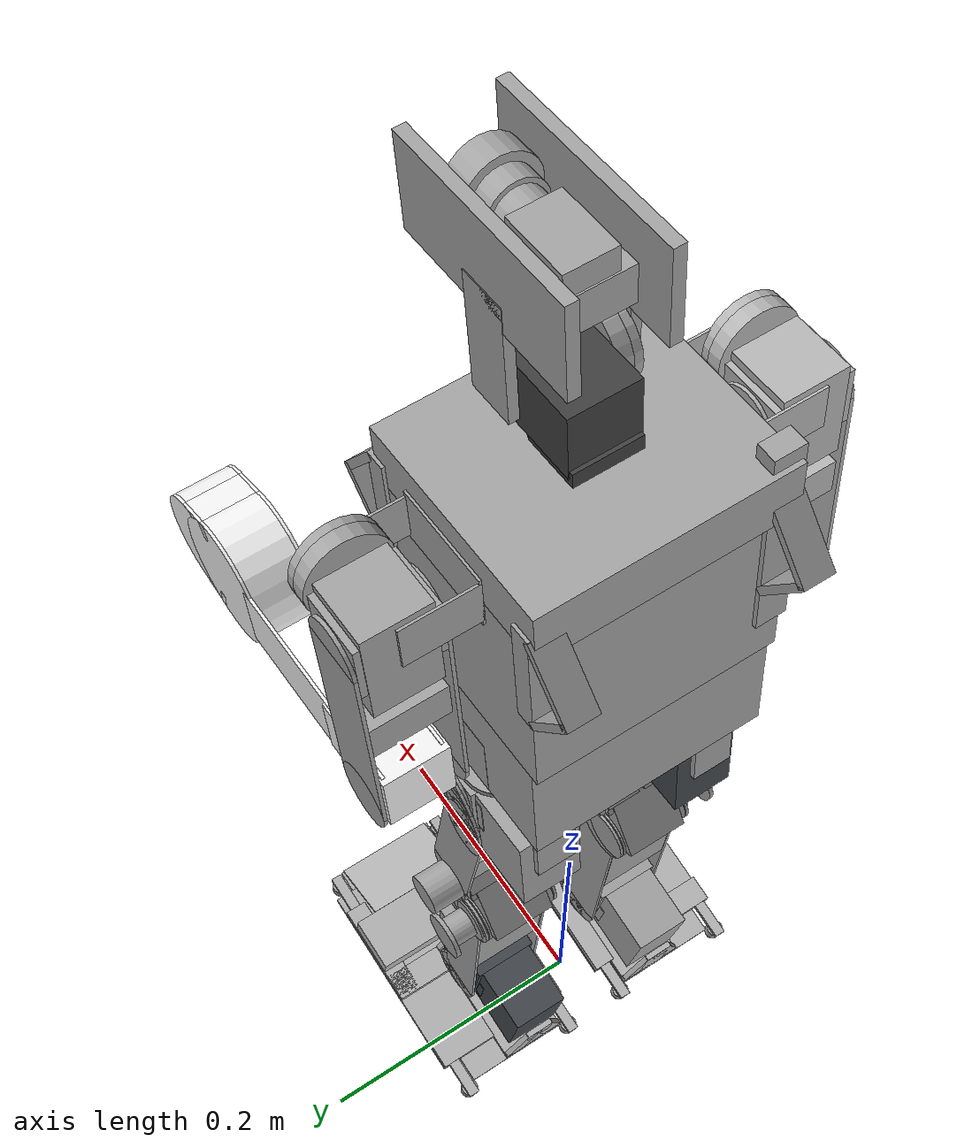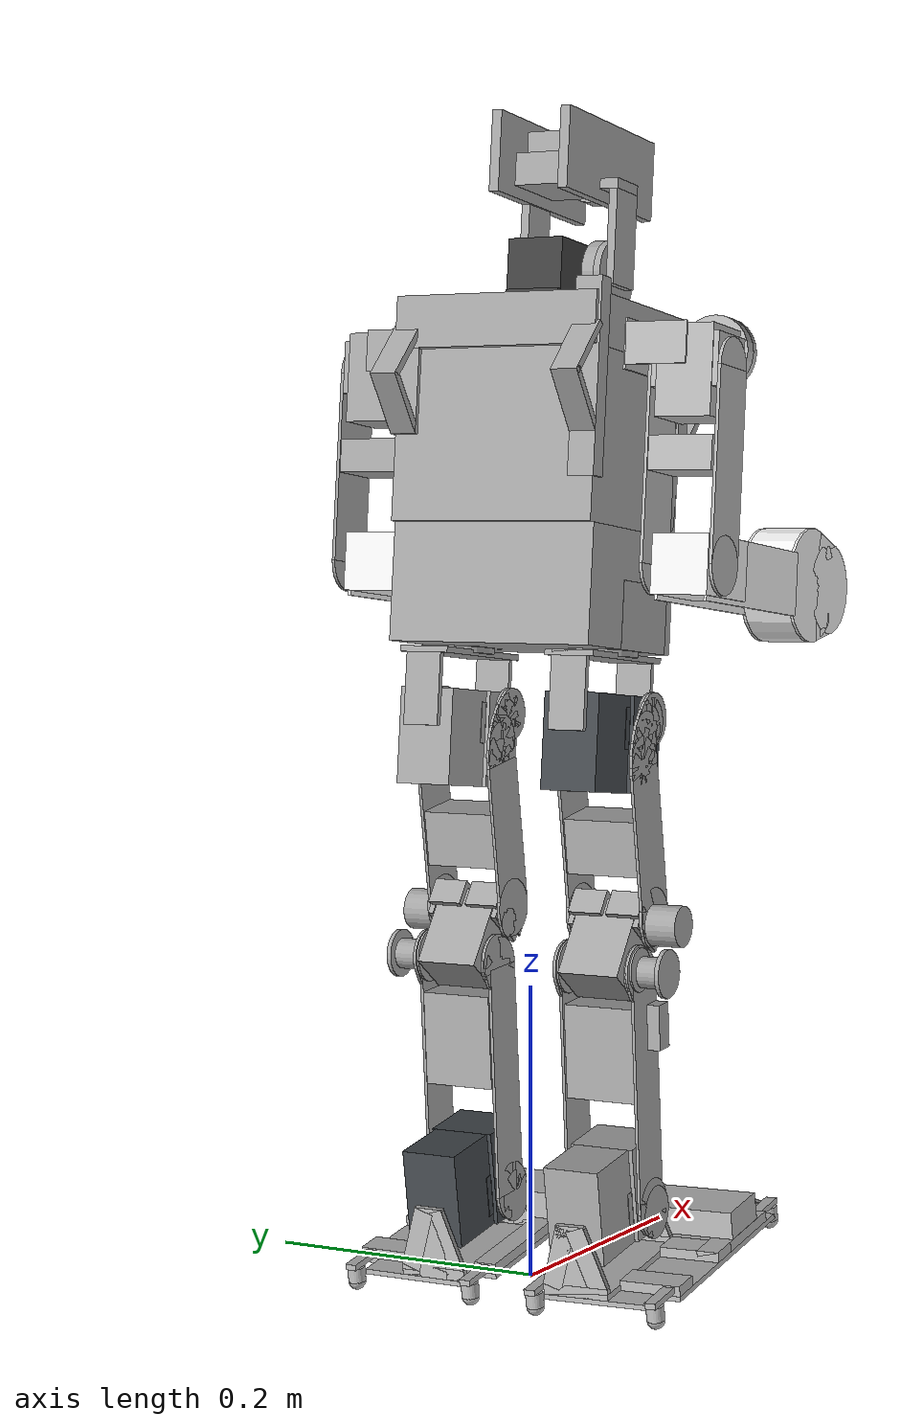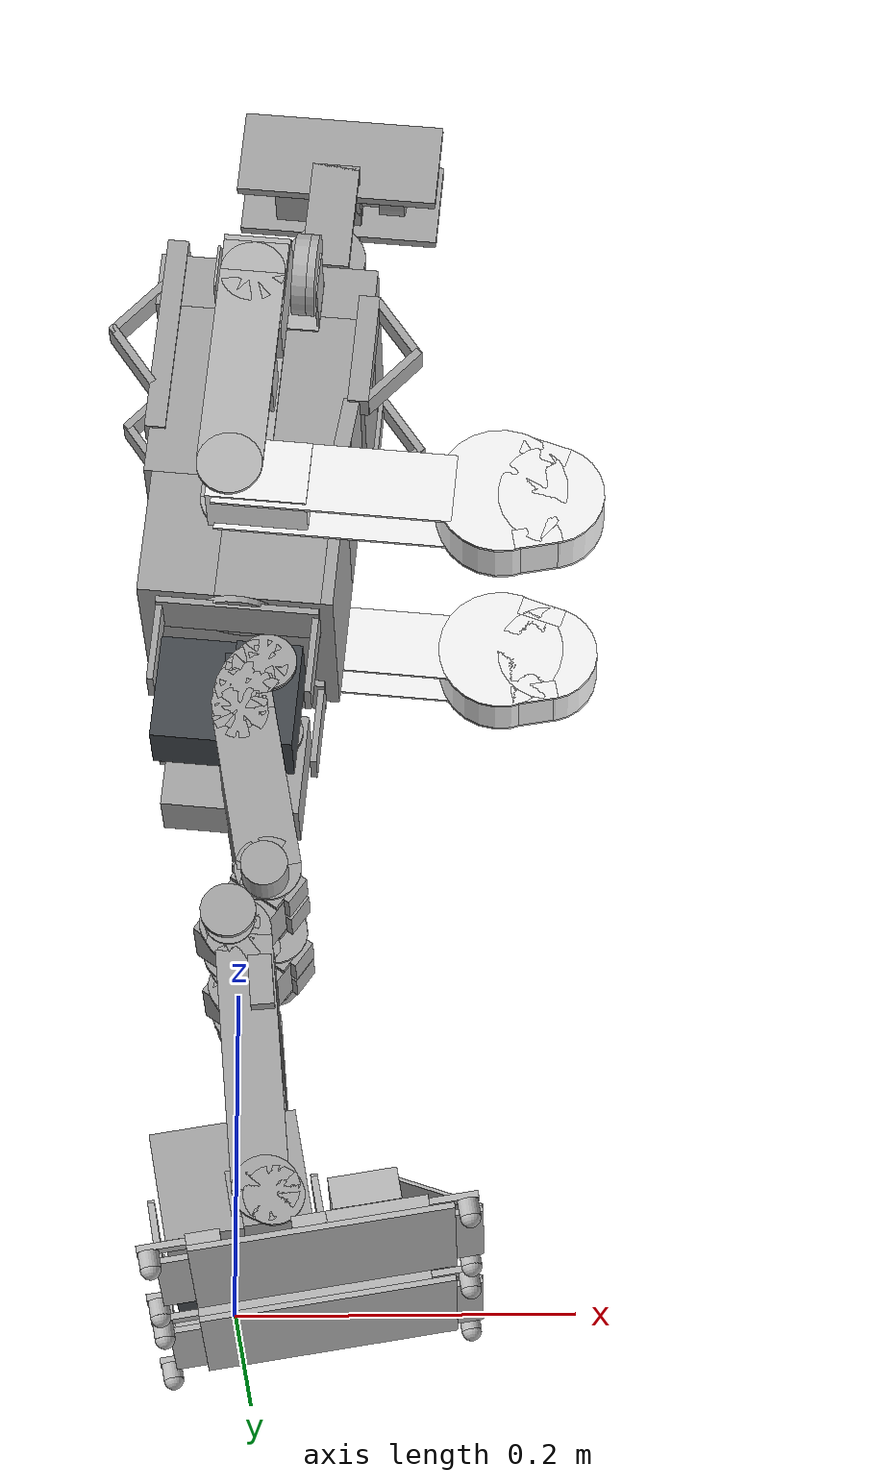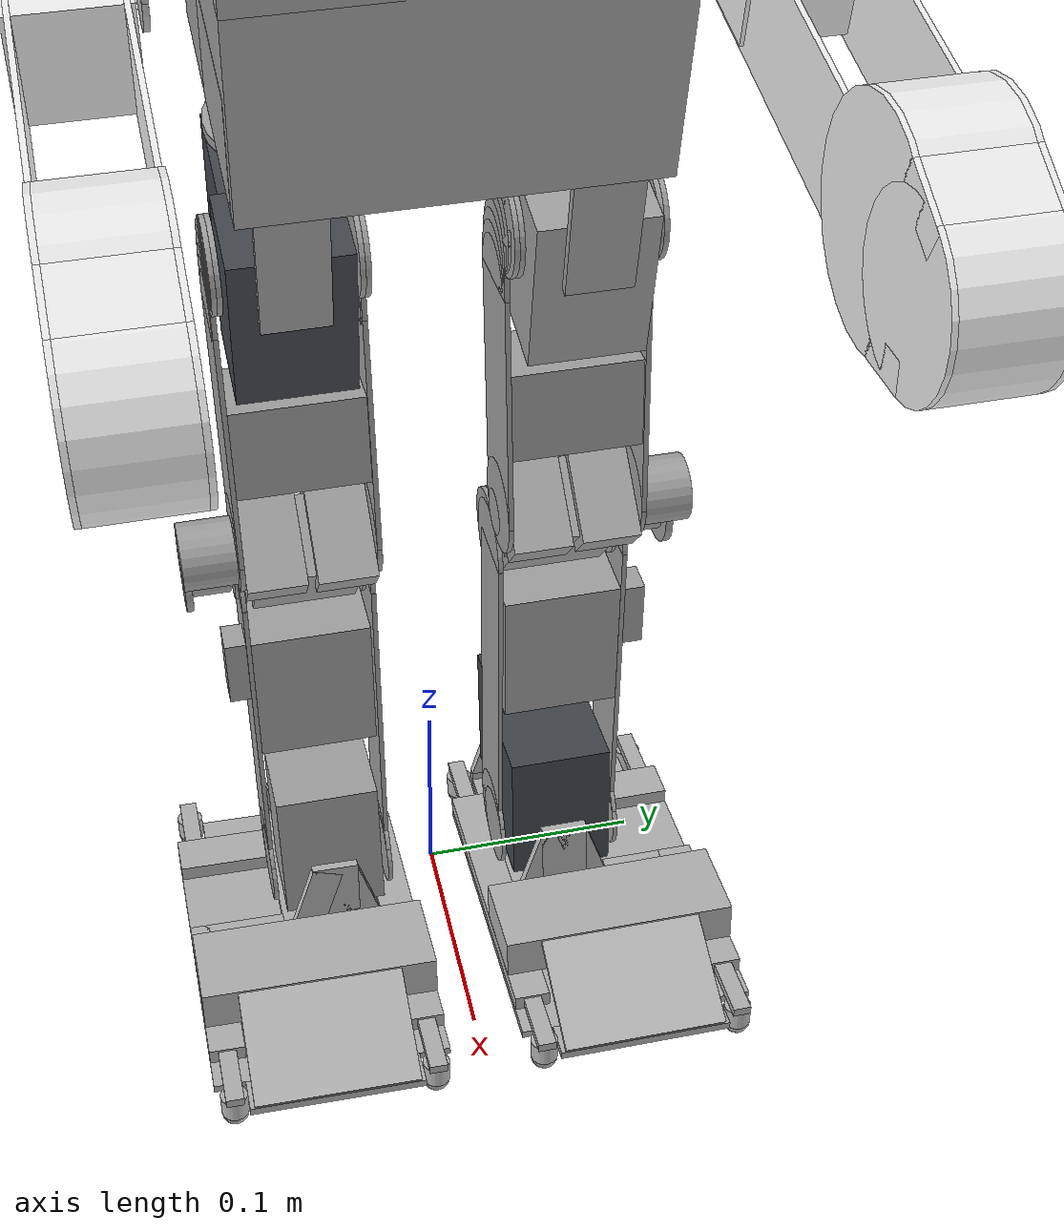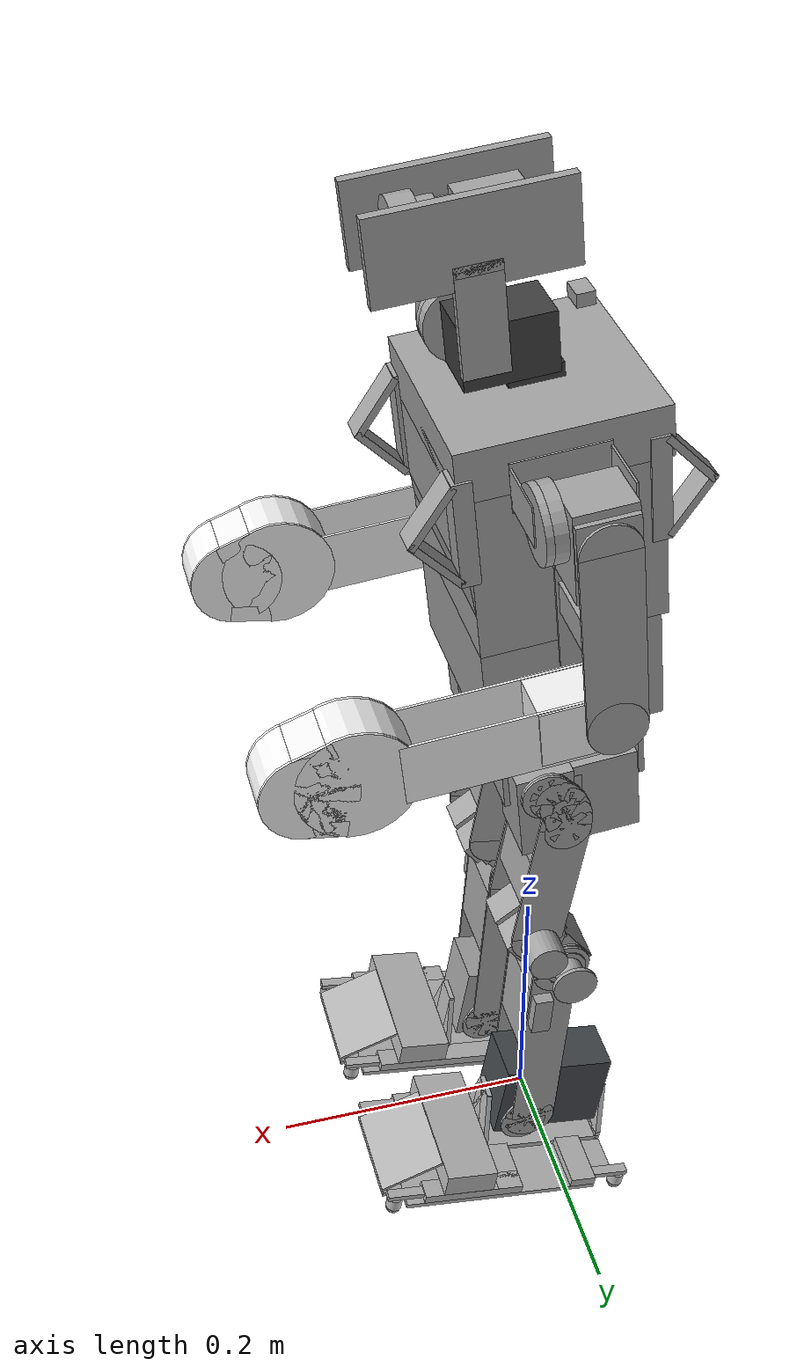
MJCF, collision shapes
<mujoco model="wolfgang">
  <compiler angle="radian" autolimits="true"/>

  <option iterations="3" ls_iterations="5" timestep="0.002" integrator="Euler">
    <flag eulerdamp="disable"/>
  </option>

  <default>
    <default class="humanoid">
      <default class="collision">
        <geom group="3" contype="1" conaffinity="1" />
      </default>
      <default class="visual">
        <geom material="black" contype="0" conaffinity="0" group="2" />
      </default>
      <default class="mx106">
        <joint damping="1.7" armature="0.025" frictionloss="0.1" />
        <position kp="45.0" ctrlrange="-3.141592 3.141592" forcerange="-12 12" />
      </default>
      <default class="mx64">
        <joint damping="0.66" armature="0.012" frictionloss="0.09" />
        <position kp="25.5" ctrlrange="-3.141592 3.141592" forcerange="-12 12" />
      </default>
      <default class="xh-540">
        <joint damping="1.7" armature="0.025" frictionloss="0.1" />
        <position kp="45.0" ctrlrange="-3.141592 3.141592" forcerange="-12 12" />
      </default>
      <site size="0.01" rgba="1 0 0 1" group="4"/>
    </default>
  </default>

  <asset>
    <mesh name="mx-64-body" file="assets/mx-64-body.stl"/>
    <mesh name="nuc_holder_right_front" file="assets/nuc_holder_right_front.stl"/>
    <mesh name="torso_bumper_right" file="assets/torso_bumper_right.stl"/>
    <mesh name="core" file="assets/core.stl"/>
    <mesh name="battery" file="assets/battery.stl"/>
    <mesh name="mx-106_body" file="assets/mx-106_body.stl"/>
    <mesh name="torso_bumper_left" file="assets/torso_bumper_left.stl"/>
    <mesh name="nuc_holder_right_back" file="assets/nuc_holder_right_back.stl"/>
    <mesh name="battery_clip" file="assets/battery_clip.stl"/>
    <mesh name="nuc_holder_left_back" file="assets/nuc_holder_left_back.stl"/>
    <mesh name="imu_holder" file="assets/imu_holder.stl"/>
    <mesh name="torso_bottom" file="assets/torso_bottom.stl"/>
    <mesh name="speaker_holder" file="assets/speaker_holder.stl"/>
    <mesh name="nuc_main" file="assets/nuc_main.stl"/>
    <mesh name="torso_top" file="assets/torso_top.stl"/>
    <mesh name="baseplate_odroid_xu4_core" file="assets/baseplate_odroid_xu4_core.stl"/>
    <mesh name="dummy_speaker" file="assets/dummy_speaker.stl"/>
    <mesh name="nuc_holder_left_front" file="assets/nuc_holder_left_front.stl"/>
    <mesh name="battery_cage" file="assets/battery_cage.stl"/>
    <mesh name="sea_connector" file="assets/sea_connector.stl"/>
    <mesh name="sea_ninjaflex" file="assets/sea_ninjaflex.stl"/>
    <mesh name="shoulder_connector" file="assets/shoulder_connector.stl"/>
    <mesh name="upper_arm" file="assets/upper_arm.stl"/>
    <mesh name="connector_shoulder" file="assets/connector_shoulder.stl"/>
    <mesh name="upper_arm_spacer" file="assets/upper_arm_spacer.stl"/>
    <mesh name="lower_arm" file="assets/lower_arm.stl"/>
    <mesh name="hand" file="assets/hand.stl"/>
    <mesh name="hip_u_connector" file="assets/hip_u_connector.stl"/>
    <mesh name="motor_connector" file="assets/motor_connector.stl"/>
    <mesh name="thrustbearingholder" file="assets/thrustbearingholder.stl"/>
    <mesh name="knee_connector" file="assets/knee_connector.stl"/>
    <mesh name="upper_leg" file="assets/upper_leg.stl"/>
    <mesh name="xh-540" file="assets/xh-540.stl"/>
    <mesh name="spring_holder_upper" file="assets/spring_holder_upper.stl"/>
    <mesh name="upper_leg_spacer" file="assets/upper_leg_spacer.stl"/>
    <mesh name="knee_spacer" file="assets/knee_spacer.stl"/>
    <mesh name="lower_leg" file="assets/lower_leg.stl"/>
    <mesh name="lower_leg_spacer" file="assets/lower_leg_spacer.stl"/>
    <mesh name="springholder_new" file="assets/springholder_new.stl"/>
    <mesh name="spring_holder_lower" file="assets/spring_holder_lower.stl"/>
    <mesh name="springholder_bottom" file="assets/springholder_bottom.stl"/>
    <mesh name="load_cell" file="assets/load_cell.stl"/>
    <mesh name="ankle" file="assets/ankle.stl"/>
    <mesh name="foot_printed_right" file="assets/foot_printed_right.stl"/>
    <mesh name="foot_cover" file="assets/foot_cover.stl"/>
    <mesh name="flex_stollen" file="assets/flex_stollen.stl"/>
    <mesh name="foot_printed_left" file="assets/foot_printed_left.stl"/>
    <mesh name="lense" file="assets/lense.stl"/>
    <mesh name="camera_side_basler_wolfgang_v2.2_right" file="assets/camera_side_basler_wolfgang_v2.2_right.stl"/>
    <mesh name="camera_side_basler_wolfgang_v2.2_left" file="assets/camera_side_basler_wolfgang_v2.2_left.stl"/>
    <mesh name="basler_ace_gige_c-mount_v01" file="assets/basler_ace_gige_c-mount_v01.stl"/>
    <mesh name="camera_lower_basler_wolfgang_imu_v2.2" file="assets/camera_lower_basler_wolfgang_imu_v2.2.stl"/>
    <material name="black" rgba="0.2 0.2 0.2 1"/>
  </asset>

  <worldbody>
    <body name="torso" pos="0.0 0.0 0.4274" quat="0.999 0.0 0.05 0.0" childclass="humanoid" >
      <freejoint/>
      <site name="imu"/>
      <inertial pos="-0.00564376 -0.0026297 0.109553" quat="0.997756 0.00472747 0.0649963 -0.0153334" mass="3.0839" diaginertia="0.0185762 0.0158759 0.00761796"/>
      <geom pos="-0.0015 0.053 0.2035" quat="9.38184e-07 -0.707105 9.38187e-07 0.707108" type="mesh" mesh="mx-64-body" class="visual"/>
      <geom size="0.0201 0.0205 0.03055" pos="0.01605 0.053 0.2035" quat="9.38184e-07 -0.707105 9.38187e-07 0.707108" type="box" rgba="0.647059 0.647059 0.647059 1" class="collision"/>
      <geom pos="-0.0015 -0.053 0.2035" quat="0.707105 0 -0.707108 0" type="mesh" mesh="mx-64-body" class="visual"/>
      <geom size="0.0201 0.0205 0.03055" pos="0.01605 -0.053 0.2035" quat="0.707105 0 -0.707108 0" type="box" rgba="0.647059 0.647059 0.647059 1" class="collision"/>
      <geom pos="-0.01485 -0.059 0.152" quat="0.707105 0 0 0.707108" type="mesh" mesh="nuc_holder_right_front" class="visual"/>
      <geom pos="-0.057 0.077 0.213915" quat="0.499998 -0.5 -0.500002 0.5" type="mesh" mesh="torso_bumper_right" class="visual"/>
      <geom size="0.0095 0.0365 0.0065" pos="-0.0635 0.0675 0.177415" quat="0.499998 -0.5 -0.500002 0.5" type="box" rgba="0.647059 0.647059 0.647059 1" class="collision"/>
      <geom size="0.0095 0.0234397 0.0025" pos="-0.0831853 0.0675 0.193936" quat="0.30209 0.639328 0.63933 0.302091" type="box" rgba="0.647059 0.647059 0.647059 1" class="collision"/>
      <geom size="0.0095 0.0234397 0.0025" pos="-0.0831853 0.0675 0.160894" quat="0.30209 -0.639328 -0.63933 0.302091" type="box" rgba="0.647059 0.647059 0.647059 1" class="collision"/>
      <geom pos="-0.01 0.001 0.118" quat="0.707105 0 0 -0.707108" type="mesh" mesh="core" class="visual"/>
      <geom pos="-0.0175 -0.0035 0.0295" quat="0.707105 0 0 -0.707108" type="mesh" mesh="battery" class="visual"/>
      <geom size="0.07 0.02 0.022" pos="-0.0375 -0.0035 0.0295" quat="0.707105 0 0 -0.707108" type="box" rgba="0.647059 0.647059 0.647059 1" class="collision"/>
      <geom pos="0 -0.055 0.026" quat="0.499998 0.5 -0.500002 -0.5" type="mesh" mesh="mx-106_body" class="visual"/>
      <geom size="0.0201 0.023 0.03255" pos="0.01805 -0.055 0.026" quat="0.499998 0.5 -0.500002 -0.5" type="box" rgba="0.647059 0.647059 0.647059 1" class="collision"/>
      <geom pos="0.053 0.077 0.213915" quat="0.499998 -0.5 0.500002 -0.5" type="mesh" mesh="torso_bumper_left" class="visual"/>
      <geom size="0.0095 0.0365 0.0065" pos="0.0595 0.0675 0.177415" quat="0.499998 -0.5 0.500002 -0.5" type="box" rgba="0.647059 0.647059 0.647059 1" class="collision"/>
      <geom size="0.0095 0.0234397 0.0025" pos="0.0791853 0.0675 0.193936" quat="0.30209 0.639328 -0.63933 -0.302091" type="box" rgba="0.647059 0.647059 0.647059 1" class="collision"/>
      <geom size="0.0095 0.0234397 0.0025" pos="0.0791853 0.0675 0.160894" quat="0.30209 -0.639328 0.63933 -0.302091" type="box" rgba="0.647059 0.647059 0.647059 1" class="collision"/>
      <geom pos="-0.04715 -0.0589 0.152" quat="0.707105 0 0 0.707108" type="mesh" mesh="nuc_holder_right_back" class="visual"/>
      <geom pos="0 0.055 0.026" quat="0.499998 0.5 -0.500002 -0.5" type="mesh" mesh="mx-106_body" class="visual"/>
      <geom size="0.0201 0.023 0.03255" pos="0.01805 0.055 0.026" quat="0.499998 0.5 -0.500002 -0.5" type="box" rgba="0.647059 0.647059 0.647059 1" class="collision"/>
      <geom pos="-0.0375 -0.00925 0.0295" quat="0.707105 0 0 0.707108" type="mesh" mesh="battery_clip" class="visual"/>
      <geom pos="-0.04715 0.0359 0.149" quat="0.707105 0 0 0.707108" type="mesh" mesh="nuc_holder_left_back" class="visual"/>
      <geom pos="-0.0015 -0.036 0.2035" quat="9.38184e-07 -0.707105 9.38187e-07 0.707108" type="mesh" mesh="imu_holder" class="visual"/>
      <geom pos="-0.062 0.075 0.003" type="mesh" mesh="torso_bottom" class="visual"/>
      <geom size="0.06 0.075 0.04" pos="-0.002 0 0.043" type="box" rgba="0.647059 0.647059 0.647059 1" class="collision"/>
      <geom pos="-0.0095 0 0.211" quat="0.499998 -0.5 -0.500002 0.5" type="mesh" mesh="mx-64-body" class="visual"/>
      <geom size="0.0201 0.0205 0.03055" pos="0.00805 0 0.211" quat="0.499998 -0.5 -0.500002 0.5" type="box" rgba="0.647059 0.647059 0.647059 1" class="collision"/>
      <geom pos="-0.057 -0.077 0.213915" quat="0.499998 -0.5 -0.500002 0.5" type="mesh" mesh="torso_bumper_left" class="visual"/>
      <geom size="0.0095 0.065 0.0065" pos="-0.0635 -0.0675 0.177415" quat="0.499998 -0.5 -0.500002 0.5" type="box" rgba="0.647059 0.647059 0.647059 1" class="collision"/>
      <geom size="0.0095 0.0234397 0.0025" pos="-0.0831853 -0.0675 0.193936" quat="0.30209 0.639328 0.63933 0.302091" type="box" rgba="0.647059 0.647059 0.647059 1" class="collision"/>
      <geom size="0.0095 0.0234397 0.0025" pos="-0.0831853 -0.0675 0.160894" quat="0.30209 -0.639328 -0.63933 0.302091" type="box" rgba="0.647059 0.647059 0.647059 1" class="collision"/>
      <geom pos="0.03 0 0.006" quat="0.707105 0 0 0.707108" type="mesh" mesh="speaker_holder" class="visual"/>
      <geom pos="-0.002 -0.0115 0.152" quat="0.707105 0 0 0.707108" type="mesh" mesh="nuc_main" class="visual"/>
      <geom pos="0.053 -0.077 0.213915" quat="0.499998 -0.5 0.500002 -0.5" type="mesh" mesh="torso_bumper_right" class="visual"/>
      <geom size="0.0095 0.0365 0.0065" pos="0.0595 -0.0675 0.177415" quat="0.499998 -0.5 0.500002 -0.5" type="box" rgba="0.647059 0.647059 0.647059 1" class="collision"/>
      <geom size="0.0095 0.0234397 0.0025" pos="0.0791853 -0.0675 0.193936" quat="0.30209 0.639328 -0.63933 -0.302091" type="box" rgba="0.647059 0.647059 0.647059 1" class="collision"/>
      <geom size="0.0095 0.0234397 0.0025" pos="0.0791853 -0.0675 0.160894" quat="0.30209 -0.639328 0.63933 -0.302091" type="box" rgba="0.647059 0.647059 0.647059 1" class="collision"/>
      <geom pos="-0.077 -0.075 0.083" quat="0.707105 0 0 0.707108" type="mesh" mesh="torso_top" class="visual"/>
      <geom pos="-0.002 0 0.088" quat="0.707105 0 0 -0.707108" type="mesh" mesh="baseplate_odroid_xu4_core" class="visual"/>
      <geom size="0.075 0.0625 0.0575" pos="-0.0045 0 0.1405" quat="0.707105 0 0 0.707108" type="box" rgba="0.647059 0.647059 0.647059 1" class="collision"/>
      <geom size="0.075 0.005 0.0273829" pos="0.053 0 0.115383" quat="0.706352 0.0326317 0.0326318 0.706355" type="box" rgba="0.647059 0.647059 0.647059 1" class="collision"/>
      <geom size="0.075 0.005 0.0327252" pos="0.058 0 0.175725" quat="0.707105 0 0 0.707108" type="box" rgba="0.647059 0.647059 0.647059 1" class="collision"/>
      <geom size="0.075 0.068 0.0175" pos="-0.005 0 0.2155" quat="0.707105 0 0 0.707108" type="box" rgba="0.647059 0.647059 0.647059 1" class="collision"/>
      <geom pos="0.0314886 0 0.011" quat="0.707105 0 0 0.707108" type="mesh" mesh="dummy_speaker" class="visual"/>
      <geom pos="-0.01485 0.036 0.149" quat="0.707105 0 0 0.707108" type="mesh" mesh="nuc_holder_left_front" class="visual"/>
      <geom pos="-0.0375 -0.00925 0.0295" quat="0.707105 0 0 0.707108" type="mesh" mesh="battery_cage" class="visual"/>
      <body name="r_shoulder" pos="-0.0015 -0.0765 0.2035" quat="1.32679e-06 0 0 -1">
        <inertial pos="-0.0135397 0.0284022 -1.54699e-06" quat="0.180501 0.68368 -0.180422 0.683703" mass="0.041445" diaginertia="3.49573e-05 3.19948e-05 1.42174e-05" />
        <joint name="RShoulderPitch" pos="0 0 0" axis="0 1 0" range="-3.14159 3.14159" class="mx106"/>
        <geom pos="-0.02595 0.042 0" quat="0.499998 -0.5 -0.500002 0.5" type="mesh" mesh="sea_connector" class="visual"/>
        <geom size="0.025 0.0025" pos="-0.02845 0.042 0" quat="0.499998 -0.5 -0.500002 0.5" type="cylinder" rgba="0.717647 0.717647 0.717647 1" class="collision"/>
        <geom pos="-0.01695 0.042 0" quat="0.499998 -0.5 -0.500002 0.5" type="mesh" mesh="sea_ninjaflex" class="visual"/>
        <geom size="0.025 0.0045" pos="-0.02145 0.042 0" quat="0.499998 -0.5 -0.500002 0.5" type="cylinder" rgba="0.717647 0.717647 0.717647 1" class="collision"/>
        <geom type="mesh" mesh="shoulder_connector" class="visual"/>
        <geom size="0.03195 0.00075 0.017" pos="0 0.00075 0" type="box" rgba="0.717647 0.717647 0.717647 1" class="collision"/>
        <geom size="0.00075 0.0225 0.014" pos="0.0312 0.0225 0" type="box" rgba="0.717647 0.717647 0.717647 1" class="collision"/>
        <geom size="0.00075 0.0225 0.014" pos="-0.0312 0.0225 0" type="box" rgba="0.717647 0.717647 0.717647 1" class="collision"/>
        <body name="r_upper_arm" pos="-0.01695 0.042 0" quat="0.499998 0.5 -0.500002 -0.5">
          <inertial pos="9.77435e-05 -0.0325821 -0.0239229" quat="0.493157 0.506993 -0.500259 0.499495" mass="0.228498" diaginertia="0.000371168 0.000241466 0.00017944" />
          <joint name="RShoulderRoll" pos="0 0 0" axis="0 0 -1" range="0 3.14159" class="mx106"/>
          <geom pos="0 0 -0.0235" quat="0.707105 -0.707108 0 0" type="mesh" mesh="mx-64-body" class="visual"/>
          <geom size="0.0201 0.0205 0.03055" pos="0 -0.01755 -0.0235" quat="0.707105 -0.707108 0 0" type="box" rgba="0.717647 0.717647 0.717647 1" class="collision"/>
          <geom pos="0.0265 -0.144 -0.0235" quat="0.499998 -0.5 -0.5 -0.500002" type="mesh" mesh="upper_arm" class="visual"/>
          <geom size="0.02 0.001125" pos="0.025125 -0.144 -0.0235" quat="0.707105 0 -0.707108 0" type="cylinder" rgba="0.717647 0.717647 0.717647 1" class="collision"/>
          <geom size="0.02 0.001125" pos="0.025125 -0.014 -0.0235" quat="0.707105 0 -0.707108 0" type="cylinder" rgba="0.717647 0.717647 0.717647 1" class="collision"/>
          <geom size="0.02 0.001125 0.065" pos="0.025125 -0.079 -0.0235" quat="0.499998 -0.5 -0.5 -0.500002" type="box" rgba="0.717647 0.717647 0.717647 1" class="collision"/>
          <geom pos="-0.0147 -0.0105 -0.0235" quat="0.499998 -0.5 -0.500002 0.5" type="mesh" mesh="connector_shoulder" class="visual"/>
          <geom size="0.018 0.02 0.00465" pos="-0.01935 -0.0105 -0.0235" quat="0.499998 -0.5 -0.500002 0.5" type="box" rgba="0.717647 0.717647 0.717647 1" class="collision"/>
          <geom pos="-0.0265 -0.144 -0.0235" quat="0.499998 -0.5 0.5 0.500002" type="mesh" mesh="upper_arm" class="visual"/>
          <geom size="0.02 0.001125" pos="-0.025125 -0.144 -0.0235" quat="0.707105 0 0.707108 0" type="cylinder" rgba="0.717647 0.717647 0.717647 1" class="collision"/>
          <geom size="0.02 0.001125" pos="-0.025125 -0.014 -0.0235" quat="0.707105 0 0.707108 0" type="cylinder" rgba="0.717647 0.717647 0.717647 1" class="collision"/>
          <geom size="0.02 0.001125 0.065" pos="-0.025125 -0.079 -0.0235" quat="0.499998 -0.5 0.5 0.500002" type="box" rgba="0.717647 0.717647 0.717647 1" class="collision"/>
          <geom pos="0.0147 -0.0105 -0.0235" quat="0.499998 0.5 0.500002 0.5" type="mesh" mesh="connector_shoulder" class="visual"/>
          <geom size="0.018 0.02 0.00465" pos="0.01935 -0.0105 -0.0235" quat="0.499998 0.5 0.500002 0.5" type="box" rgba="0.717647 0.717647 0.717647 1" class="collision"/>
          <geom pos="0.024 -0.064 -0.038499" quat="0.707105 0 -0.707108 0" type="mesh" mesh="upper_arm_spacer" class="visual"/>
          <geom size="0.0188 0.0115 0.023" pos="0.001 -0.0715 -0.023699" quat="0.707105 0 -0.707108 0" type="box" rgba="0.717647 0.717647 0.717647 1" class="collision"/>
            <body name="r_lower_arm" pos="0.024 -0.144 -0.0235" quat="0.499998 -0.5 0.500002 -0.5">
            <inertial pos="0.000436307 -0.0605126 -0.0235553" quat="0.500185 0.49962 -0.500396 0.499799" mass="0.207774" diaginertia="0.00110076 0.001088 8.9031e-05" />
            <joint name="RElbow" pos="0 0 0" axis="0 0 1" range="-1.0472 1.5708" class="mx64"/>
            <geom pos="0 -0.163682 -0.0065" quat="9.38184e-07 -9.38187e-07 0.707108 -0.707105" type="mesh" mesh="lower_arm" class="visual"/>
            <geom size="0.04 0.001" pos="0 -0.163682 -0.0055" quat="1.32679e-06 0 0 -1" type="cylinder" rgba="0.960784 0.960784 0.960784 1" class="collision"/>
            <geom size="0.022 0.001 0.0725" pos="0.0015 -0.0631823 -0.0055" quat="9.38184e-07 -9.38187e-07 0.707108 -0.707105" type="box" rgba="0.960784 0.960784 0.960784 1" class="collision"/>
            <geom size="0.032 0.001" pos="0 -0.193682 -0.0055" quat="1.32679e-06 0 0 -1" type="cylinder" rgba="0.960784 0.960784 0.960784 1" class="collision"/>
            <geom size="0.006 0.001 0.0145" pos="-0.0282 -0.187682 -0.0055" quat="0.701469 -0.701472 -0.0891014 0.089101" type="box" rgba="0.960784 0.960784 0.960784 1" class="collision"/>
            <geom size="0.006 0.001 0.0145" pos="0.0282 -0.187682 -0.0055" quat="0.701469 -0.701472 0.0891014 -0.089101" type="box" rgba="0.960784 0.960784 0.960784 1" class="collision"/>
            <geom pos="0 0 -0.0235" quat="0.707105 -0.707108 0 0" type="mesh" mesh="mx-64-body" class="visual"/>
            <geom size="0.0201 0.0205 0.03055" pos="0 -0.01755 -0.0235" quat="0.707105 -0.707108 0 0" type="box" rgba="0.960784 0.960784 0.960784 1" class="collision"/>
            <geom pos="0 -0.163682 -0.0065" quat="0.707105 0.707108 0 0" type="mesh" mesh="hand" class="visual"/>
            <geom size="0.04 0.017" pos="0 -0.163682 -0.0235" quat="1.32679e-06 -1 0 0" type="cylinder" rgba="0.960784 0.960784 0.960784 1" class="collision"/>
            <geom size="0.032 0.017" pos="0 -0.193682 -0.0235" quat="1.32679e-06 -1 0 0" type="cylinder" rgba="0.960784 0.960784 0.960784 1" class="collision"/>
            <geom size="0.006 0.017 0.0145" pos="0.0282 -0.187682 -0.0235" quat="0.0891027 0.089103 0.701472 0.701469" type="box" rgba="0.960784 0.960784 0.960784 1" class="collision"/>
            <geom size="0.006 0.017 0.0145" pos="-0.0282 -0.187682 -0.0235" quat="0.0891027 0.089103 -0.701472 -0.701469" type="box" rgba="0.960784 0.960784 0.960784 1" class="collision"/>
            <geom pos="0 -0.163682 -0.0425" quat="9.38184e-07 -9.38187e-07 0.707108 -0.707105" type="mesh" mesh="lower_arm" class="visual"/>
            <geom size="0.04 0.001" pos="0 -0.163682 -0.0415" quat="1.32679e-06 0 0 -1" type="cylinder" rgba="0.960784 0.960784 0.960784 1" class="collision"/>
            <geom size="0.022 0.001 0.0725" pos="0.0015 -0.0631823 -0.0415" quat="9.38184e-07 -9.38187e-07 0.707108 -0.707105" type="box" rgba="0.960784 0.960784 0.960784 1" class="collision"/>
            <geom size="0.032 0.001" pos="0 -0.193682 -0.0415" quat="1.32679e-06 0 0 -1" type="cylinder" rgba="0.960784 0.960784 0.960784 1" class="collision"/>
            <geom size="0.006 0.001 0.0145" pos="-0.0282 -0.187682 -0.0415" quat="0.701469 -0.701472 -0.0891014 0.089101" type="box" rgba="0.960784 0.960784 0.960784 1" class="collision"/>
            <geom size="0.006 0.001 0.0145" pos="0.0282 -0.187682 -0.0415" quat="0.701469 -0.701472 0.0891014 -0.089101" type="box" rgba="0.960784 0.960784 0.960784 1" class="collision"/>
          </body>
        </body>
      </body>
      <body name="l_shoulder" pos="-0.0015 0.0765 0.2035" quat="1.7603e-12 -1.32679e-06 -1 1.32679e-06">
        <inertial pos="-0.0135397 0.0284022 1.54699e-06" quat="0.180422 0.683703 -0.180501 0.68368" mass="0.041445" diaginertia="3.49573e-05 3.19948e-05 1.42174e-05" />
        <joint name="LShoulderPitch" pos="0 0 0" axis="0 1 0" range="-3.14159 3.14159" class="mx106"/>
        <geom pos="-0.02595 0.042 0" quat="0.499998 0.5 -0.500002 -0.5" type="mesh" mesh="sea_connector" class="visual"/>
        <geom size="0.025 0.0025" pos="-0.02845 0.042 0" quat="0.499998 0.5 -0.500002 -0.5" type="cylinder" rgba="0.647059 0.647059 0.647059 1" class="collision"/>
        <geom type="mesh" mesh="shoulder_connector" class="visual"/>
        <geom size="0.03195 0.00075 0.017" pos="0 0.00075 0" type="box" rgba="0.647059 0.647059 0.647059 1" class="collision"/>
        <geom size="0.00075 0.0225 0.014" pos="0.0312 0.0225 0" type="box" rgba="0.647059 0.647059 0.647059 1" class="collision"/>
        <geom size="0.00075 0.0225 0.014" pos="-0.0312 0.0225 0" type="box" rgba="0.647059 0.647059 0.647059 1" class="collision"/>
        <geom pos="-0.01695 0.042 0" quat="0.499998 0.5 -0.500002 -0.5" type="mesh" mesh="sea_ninjaflex" class="visual"/>
        <geom size="0.025 0.0045" pos="-0.02145 0.042 0" quat="0.499998 0.5 -0.500002 -0.5" type="cylinder" rgba="0.647059 0.647059 0.647059 1" class="collision"/>
        <body name="l_upper_arm" pos="-0.01695 0.042 0" quat="0.499998 -0.5 -0.500002 0.5">
          <inertial pos="9.77435e-05 -0.0325821 -0.0239229" quat="0.493157 0.506993 -0.500259 0.499495" mass="0.228498" diaginertia="0.000371168 0.000241466 0.00017944" />
          <joint name="LShoulderRoll" pos="0 0 0" axis="0 0 -1" range="-3.14159 0" class="mx106"/>
          <geom pos="0 0 -0.0235" quat="0.707105 -0.707108 0 0" type="mesh" mesh="mx-64-body" class="visual"/>
          <geom size="0.0201 0.0205 0.03055" pos="0 -0.01755 -0.0235" quat="0.707105 -0.707108 0 0" type="box" rgba="0.647059 0.647059 0.647059 1" class="collision"/>
          <geom pos="-0.0147 -0.0105 -0.0235" quat="0.499998 -0.5 -0.500002 0.5" type="mesh" mesh="connector_shoulder" class="visual"/>
          <geom size="0.018 0.02 0.00465" pos="-0.01935 -0.0105 -0.0235" quat="0.499998 -0.5 -0.500002 0.5" type="box" rgba="0.647059 0.647059 0.647059 1" class="collision"/>
          <geom pos="0.0147 -0.0105 -0.0235" quat="0.499998 0.5 0.500002 0.5" type="mesh" mesh="connector_shoulder" class="visual"/>
          <geom size="0.018 0.02 0.00465" pos="0.01935 -0.0105 -0.0235" quat="0.499998 0.5 0.500002 0.5" type="box" rgba="0.647059 0.647059 0.647059 1" class="collision"/>
          <geom pos="0.024 -0.064 -0.038499" quat="0.707105 0 -0.707108 0" type="mesh" mesh="upper_arm_spacer" class="visual"/>
          <geom size="0.0188 0.0115 0.023" pos="0.001 -0.0715 -0.023699" quat="0.707105 0 -0.707108 0" type="box" rgba="0.647059 0.647059 0.647059 1" class="collision"/>
          <geom pos="-0.0265 -0.144 -0.0235" quat="0.499998 -0.5 0.5 0.500002" type="mesh" mesh="upper_arm" class="visual"/>
          <geom size="0.02 0.001125" pos="-0.025125 -0.144 -0.0235" quat="0.707105 0 0.707108 0" type="cylinder" rgba="0.647059 0.647059 0.647059 1" class="collision"/>
          <geom size="0.02 0.001125" pos="-0.025125 -0.014 -0.0235" quat="0.707105 0 0.707108 0" type="cylinder" rgba="0.647059 0.647059 0.647059 1" class="collision"/>
          <geom size="0.02 0.001125 0.065" pos="-0.025125 -0.079 -0.0235" quat="0.499998 -0.5 0.5 0.500002" type="box" rgba="0.647059 0.647059 0.647059 1" class="collision"/>
          <geom pos="0.0265 -0.144 -0.0235" quat="0.499998 -0.5 -0.5 -0.500002" type="mesh" mesh="upper_arm" class="visual"/>
          <geom size="0.02 0.001125" pos="0.025125 -0.144 -0.0235" quat="0.707105 0 -0.707108 0" type="cylinder" rgba="0.647059 0.647059 0.647059 1" class="collision"/>
          <geom size="0.02 0.001125" pos="0.025125 -0.014 -0.0235" quat="0.707105 0 -0.707108 0" type="cylinder" rgba="0.647059 0.647059 0.647059 1" class="collision"/>
          <geom size="0.02 0.001125 0.065" pos="0.025125 -0.079 -0.0235" quat="0.499998 -0.5 -0.5 -0.500002" type="box" rgba="0.647059 0.647059 0.647059 1" class="collision"/>
          <body name="l_lower_arm" pos="-0.024 -0.144 -0.0235" quat="0.499998 -0.5 -0.500002 0.5">
            <inertial pos="-0.000436306 -0.0605126 -0.0235553" quat="0.502963 0.497233 -0.502767 0.497003" mass="0.207774" diaginertia="0.00110076 0.00108813 8.89004e-05" />
            <joint name="LElbow" pos="0 0 0" axis="0 0 1" range="-1.5708 1.0472" class="mx64"/>
            <geom pos="0 0 -0.0235" quat="0.707105 -0.707108 0 0" type="mesh" mesh="mx-64-body" class="visual"/>
            <geom size="0.0201 0.0205 0.03055" pos="0 -0.01755 -0.0235" quat="0.707105 -0.707108 0 0" type="box" rgba="0.960784 0.960784 0.960784 1" class="collision"/>
            <geom pos="0 -0.163682 -0.0405" quat="0.707105 0.707108 0 0" type="mesh" mesh="lower_arm" class="visual"/>
            <geom size="0.04 0.001" pos="0 -0.163682 -0.0415" quat="1.32679e-06 -1 0 0" type="cylinder" rgba="0.960784 0.960784 0.960784 1" class="collision"/>
            <geom size="0.022 0.001 0.0725" pos="-0.0015 -0.0631823 -0.0415" quat="0.707105 0.707108 0 0" type="box" rgba="0.960784 0.960784 0.960784 1" class="collision"/>
            <geom size="0.032 0.001" pos="0 -0.193682 -0.0415" quat="1.32679e-06 -1 0 0" type="cylinder" rgba="0.960784 0.960784 0.960784 1" class="collision"/>
            <geom size="0.006 0.001 0.0145" pos="0.0282 -0.187682 -0.0415" quat="0.0891027 0.089103 0.701472 0.701469" type="box" rgba="0.960784 0.960784 0.960784 1" class="collision"/>
            <geom size="0.006 0.001 0.0145" pos="-0.0282 -0.187682 -0.0415" quat="0.0891027 0.089103 -0.701472 -0.701469" type="box" rgba="0.960784 0.960784 0.960784 1" class="collision"/>
            <geom pos="0 -0.163682 -0.0405" quat="9.38184e-07 -9.38187e-07 0.707108 -0.707105" type="mesh" mesh="hand" class="visual"/>
            <geom size="0.04 0.017" pos="0 -0.163682 -0.0235" quat="1.32679e-06 0 0 -1" type="cylinder" rgba="0.960784 0.960784 0.960784 1" class="collision"/>
            <geom size="0.032 0.017" pos="0 -0.193682 -0.0235" quat="1.32679e-06 0 0 -1" type="cylinder" rgba="0.960784 0.960784 0.960784 1" class="collision"/>
            <geom size="0.006 0.017 0.0145" pos="-0.0282 -0.187682 -0.0235" quat="0.701469 -0.701472 -0.0891014 0.089101" type="box" rgba="0.960784 0.960784 0.960784 1" class="collision"/>
            <geom size="0.006 0.017 0.0145" pos="0.0282 -0.187682 -0.0235" quat="0.701469 -0.701472 0.0891014 -0.089101" type="box" rgba="0.960784 0.960784 0.960784 1" class="collision"/>
            <geom pos="0 -0.163682 -0.0045" quat="0.707105 0.707108 0 0" type="mesh" mesh="lower_arm" class="visual"/>
            <geom size="0.04 0.001" pos="0 -0.163682 -0.0055" quat="1.32679e-06 -1 0 0" type="cylinder" rgba="0.960784 0.960784 0.960784 1" class="collision"/>
            <geom size="0.022 0.001 0.0725" pos="-0.0015 -0.0631823 -0.0055" quat="0.707105 0.707108 0 0" type="box" rgba="0.960784 0.960784 0.960784 1" class="collision"/>
            <geom size="0.032 0.001" pos="0 -0.193682 -0.0055" quat="1.32679e-06 -1 0 0" type="cylinder" rgba="0.960784 0.960784 0.960784 1" class="collision"/>
            <geom size="0.006 0.001 0.0145" pos="0.0282 -0.187682 -0.0055" quat="0.0891027 0.089103 0.701472 0.701469" type="box" rgba="0.960784 0.960784 0.960784 1" class="collision"/>
            <geom size="0.006 0.001 0.0145" pos="-0.0282 -0.187682 -0.0055" quat="0.0891027 0.089103 -0.701472 -0.701469" type="box" rgba="0.960784 0.960784 0.960784 1" class="collision"/>
          </body>
        </body>
      </body>
      <body name="r_hip_1" pos="0 -0.055 0" quat="0.707105 -0.707108 0 0">
        <inertial pos="1.20984e-11 0.010315 -1.06799e-07" quat="-6.86297e-06 0.707107 -6.86297e-06 0.707107" mass="0.0689735" diaginertia="0.000110523 0.00010714 2.18955e-05" />
        <joint name="RHipYaw" pos="0 0 0" axis="0 1 0" range="-1.5708 1.5708" class="mx106"/>
        <geom pos="0 -0.0006 -0.018" type="mesh" mesh="hip_u_connector" class="visual"/>
        <geom size="0.018 0.05 0.002" pos="0 0.0014 0" quat="0.499998 -0.5 0.5 0.500002" type="box" rgba="0.647059 0.647059 0.647059 1" class="collision"/>
        <geom size="0.0130115 0.002 0.0265" pos="-0.048 0.0259 0" quat="0.499998 -0.5 0.5 0.500002" type="box" rgba="0.647059 0.647059 0.647059 1" class="collision"/>
        <geom size="0.0130115 0.002 0.0265" pos="0.048 0.0259 0" quat="0.499998 -0.5 0.5 0.500002" type="box" rgba="0.647059 0.647059 0.647059 1" class="collision"/>
        <geom size="0.025 0.002" pos="0 -0.0006 0.002" quat="0.499998 -0.5 0.5 0.500002" type="cylinder" rgba="0.647059 0.647059 0.647059 1" class="collision"/>
          <body name="r_hip_2" pos="-0.046 0.0414 0" quat="9.38184e-07 -0.707105 9.38187e-07 0.707108">
          <inertial pos="1.38724e-05 -0.0155281 -0.0486407" quat="0.99678 0.0129755 -0.00329376 0.0790604" mass="0.319807" diaginertia="0.000268643 0.000268139 0.000121226" />
          <joint name="RHipRoll" pos="0 0 0" axis="0 0 -1" range="-1.5708 1.5708" class="mx106"/>
          <geom pos="0 0 -0.026" quat="0.707105 -0.707108 0 0" type="mesh" mesh="mx-106_body" class="visual"/>
          <geom size="0.0201 0.023 0.03255" pos="0 -0.01805 -0.026" quat="0.707105 -0.707108 0 0" type="box" rgba="0.262745 0.282353 0.301961 1" class="collision"/>
          <geom pos="-0.0145 -0.021 -0.043" quat="9.38184e-07 -0.707105 -0.707108 9.38187e-07" type="mesh" mesh="motor_connector" class="visual"/>
          <geom size="0.014 0.003 0.00285" pos="-0.0175 -0.007 -0.04585" quat="9.38184e-07 -0.707105 -0.707108 9.38187e-07" type="box" rgba="0.262745 0.282353 0.301961 1" class="collision"/>
          <geom size="0.014 0.00175 0.00295" pos="-0.01875 -0.007 -0.05165" quat="9.38184e-07 -0.707105 -0.707108 9.38187e-07" type="box" rgba="0.262745 0.282353 0.301961 1" class="collision"/>
          <geom pos="0.014 0.0105 -0.0892" quat="1.32679e-06 0 0 -1" type="mesh" mesh="thrustbearingholder" class="visual"/>
          <geom pos="0.0145 0.007 -0.043" quat="9.38184e-07 -0.707105 0.707108 -9.38187e-07" type="mesh" mesh="motor_connector" class="visual"/>
          <geom size="0.014 0.003 0.00285" pos="0.0175 -0.007 -0.04585" quat="9.38184e-07 -0.707105 0.707108 -9.38187e-07" type="box" rgba="0.262745 0.282353 0.301961 1" class="collision"/>
          <geom size="0.014 0.00175 0.00295" pos="0.01875 -0.007 -0.05165" quat="9.38184e-07 -0.707105 0.707108 -9.38187e-07" type="box" rgba="0.262745 0.282353 0.301961 1" class="collision"/>
          <geom pos="0 0 -0.0691" quat="0.499998 -0.5 -0.5 -0.500002" type="mesh" mesh="mx-106_body" class="visual"/>
          <geom size="0.0201 0.023 0.03255" pos="0 -0.01805 -0.0691" quat="0.499998 -0.5 -0.5 -0.500002" type="box" rgba="0.262745 0.282353 0.301961 1" class="collision"/>
          <body name="r_upper_leg" pos="-0.0265 0 -0.0691" quat="0.499998 -0.5 0.5 0.500002">
            <inertial pos="0.00493985 -0.0283223 -0.133144" quat="0.995752 -0.00919328 -0.0209573 0.0891915" mass="0.242311" diaginertia="0.000503914 0.000457532 0.000112612" />
            <joint name="RHipPitch" pos="0 0 0" axis="0 1 0" range="-2.0944 1.91986" class="mx106"/>
            <geom pos="0.0182355 -0.0226528 -0.130164" quat="0.183014 0.183012 -0.683014 0.683011" type="mesh" mesh="knee_connector" class="visual"/>
            <geom size="0.021 0.0089913 0.01225" pos="0.0157399 -0.04075 -0.134486" quat="0.183014 0.183012 -0.683014 0.683011" type="box" rgba="0.647059 0.647059 0.647059 1" class="collision"/>
            <geom size="0.017 0.0124063 0.002" pos="0.0140324 -0.051 -0.137444" quat="0.183014 0.183012 -0.683014 0.683011" type="box" rgba="0.647059 0.647059 0.647059 1" class="collision"/>
            <geom pos="0 0.002 0" type="mesh" mesh="upper_leg" class="visual"/>
            <geom size="0.018 0.001" pos="0 0.001 0" quat="0.707105 0.707108 0 0" type="cylinder" rgba="0.647059 0.647059 0.647059 1" class="collision"/>
            <geom size="0.01 0.001" pos="0.009329 0.001 -0.143" quat="0.707105 0.707108 0 0" type="cylinder" rgba="0.647059 0.647059 0.647059 1" class="collision"/>
            <geom size="0.02 0.001" pos="0.0148403 0.001 -0.132659" quat="0.707105 0.707108 0 0" type="cylinder" rgba="0.647059 0.647059 0.647059 1" class="collision"/>
            <geom size="0.019 0.001 0.0510495" pos="0.00259365 0.001 -0.0830903" quat="0.991445 0 -0.130526 0" type="box" rgba="0.647059 0.647059 0.647059 1" class="collision"/>
            <geom size="0.005 0.001 0.005" pos="0.00161489 0.001 -0.0253454" quat="0.130526 1.14226e-06 0.991445 1.14226e-06" type="box" rgba="0.647059 0.647059 0.647059 1" class="collision"/>
            <geom size="0.01 0.001" pos="0.009329 0.001 -0.143" quat="0.707105 0.707108 0 0" type="cylinder" rgba="0.647059 0.647059 0.647059 1" class="collision"/>
            <geom size="0.017 0.001" pos="-0.00400978 0.001 -0.00242195" quat="0.707105 0.707108 0 0" type="cylinder" rgba="0.647059 0.647059 0.647059 1" class="collision"/>
            <geom size="0.017 0.001" pos="-0.00770728 0.001 -0.00682845" quat="0.707105 0.707108 0 0" type="cylinder" rgba="0.647059 0.647059 0.647059 1" class="collision"/>
            <geom size="0.017 0.001" pos="-0.0105834 0.001 -0.0118101" quat="0.707105 0.707108 0 0" type="cylinder" rgba="0.647059 0.647059 0.647059 1" class="collision"/>
            <geom size="0.017 0.001" pos="-0.0125508 0.001 -0.0172154" quat="0.707105 0.707108 0 0" type="cylinder" rgba="0.647059 0.647059 0.647059 1" class="collision"/>
            <geom size="0.017 0.001" pos="-0.0135497 0.001 -0.0228803" quat="0.707105 0.707108 0 0" type="cylinder" rgba="0.647059 0.647059 0.647059 1" class="collision"/>
            <geom size="0.017 0.001" pos="-0.0135497 0.001 -0.0286326" quat="0.707105 0.707108 0 0" type="cylinder" rgba="0.647059 0.647059 0.647059 1" class="collision"/>
            <geom size="0.017 0.001" pos="-0.0125508 0.001 -0.0342975" quat="0.707105 0.707108 0 0" type="cylinder" rgba="0.647059 0.647059 0.647059 1" class="collision"/>
            <geom size="0.018 0.001" pos="-2.3657e-07 -0.052 -3.21056e-07" quat="0.183014 0.183012 -0.683014 0.683011" type="cylinder" rgba="0.647059 0.647059 0.647059 1" class="collision"/>
            <geom pos="-0.00392295 -0.0265 -0.169043" quat="0.183014 0.183012 -0.683014 0.683011" type="mesh" mesh="xh-540" class="visual"/>
            <geom size="0.017 0.02925 0.022" pos="0.00382705 -0.0265 -0.15562" quat="0.183014 0.183012 -0.683014 0.683011" type="box" rgba="0.647059 0.647059 0.647059 1" class="collision"/>
            <geom pos="0.014 -0.055 -0.138" quat="0.707105 0.707108 0 0" type="mesh" mesh="spring_holder_upper" class="visual"/>
            <geom size="0.014 0.011" pos="0.014 -0.066 -0.138" quat="0.707105 0.707108 0 0" type="cylinder" rgba="0.647059 0.647059 0.647059 1" class="collision"/>
            <geom size="0.018 0.001" pos="-2.3657e-07 -0.001 -3.21056e-07" quat="0.183014 0.183012 -0.683014 0.683011" type="cylinder" rgba="0.647059 0.647059 0.647059 1" class="collision"/>
            <geom pos="0 -0.053 0" quat="1 0 0 0" type="mesh" mesh="upper_leg" class="visual"/>
            <geom size="0.018 0.001" pos="0 -0.054 0" quat="0.707105 0.707108 0 0" type="cylinder" rgba="0.647059 0.647059 0.647059 1" class="collision"/>
            <geom size="0.01 0.001" pos="0.009329 -0.054 -0.143" quat="0.707105 0.707108 0 0" type="cylinder" rgba="0.647059 0.647059 0.647059 1" class="collision"/>
            <geom size="0.02 0.001" pos="0.0148403 -0.054 -0.132659" quat="0.707105 0.707108 0 0" type="cylinder" rgba="0.647059 0.647059 0.647059 1" class="collision"/>
            <geom size="0.019 0.001 0.0510495" pos="0.00259365 -0.054 -0.0830903" quat="0.991445 0 -0.130526 0" type="box" rgba="0.647059 0.647059 0.647059 1" class="collision"/>
            <geom size="0.005 0.001 0.005" pos="0.00161489 -0.054 -0.0253454" quat="0.130526 1.14226e-06 0.991445 1.14226e-06" type="box" rgba="0.647059 0.647059 0.647059 1" class="collision"/>
            <geom size="0.01 0.001" pos="0.009329 -0.054 -0.143" quat="0.707105 0.707108 0 0" type="cylinder" rgba="0.647059 0.647059 0.647059 1" class="collision"/>
            <geom size="0.017 0.001" pos="-0.00400978 -0.054 -0.00242195" quat="0.707105 0.707108 0 0" type="cylinder" rgba="0.647059 0.647059 0.647059 1" class="collision"/>
            <geom size="0.017 0.001" pos="-0.00770728 -0.054 -0.00682845" quat="0.707105 0.707108 0 0" type="cylinder" rgba="0.647059 0.647059 0.647059 1" class="collision"/>
            <geom size="0.017 0.001" pos="-0.0105834 -0.054 -0.0118101" quat="0.707105 0.707108 0 0" type="cylinder" rgba="0.647059 0.647059 0.647059 1" class="collision"/>
            <geom size="0.017 0.001" pos="-0.0125508 -0.054 -0.0172154" quat="0.707105 0.707108 0 0" type="cylinder" rgba="0.647059 0.647059 0.647059 1" class="collision"/>
            <geom size="0.017 0.001" pos="-0.0135497 -0.054 -0.0228803" quat="0.707105 0.707108 0 0" type="cylinder" rgba="0.647059 0.647059 0.647059 1" class="collision"/>
            <geom size="0.017 0.001" pos="-0.0135497 -0.054 -0.0286326" quat="0.707105 0.707108 0 0" type="cylinder" rgba="0.647059 0.647059 0.647059 1" class="collision"/>
            <geom size="0.017 0.001" pos="-0.0125508 -0.054 -0.0342975" quat="0.707105 0.707108 0 0" type="cylinder" rgba="0.647059 0.647059 0.647059 1" class="collision"/>
            <geom pos="0.0186686 -0.0303472 -0.130414" quat="0.683011 -0.683014 0.183012 0.183013" type="mesh" mesh="knee_connector" class="visual"/>
            <geom size="0.021 0.0089913 0.01225" pos="0.0161729 -0.01225 -0.134736" quat="0.683011 -0.683014 0.183012 0.183013" type="box" rgba="0.647059 0.647059 0.647059 1" class="collision"/>
            <geom size="0.017 0.0124063 0.002" pos="0.0144654 -0.00200004 -0.137694" quat="0.683011 -0.683014 0.183012 0.183013" type="box" rgba="0.647059 0.647059 0.647059 1" class="collision"/>
            <geom pos="0.0220754 -0.053 -0.0939778" quat="0.0922969 -0.0922947 0.701059 0.701056" type="mesh" mesh="upper_leg_spacer" class="visual"/>
            <geom size="0.017575 0.019 0.0265" pos="0.00281079 -0.0265 -0.0836106" quat="0.0922969 -0.0922947 0.701059 0.701056" type="box" rgba="0.647059 0.647059 0.647059 1" class="collision"/>
            <body name="r_lower_leg" pos="-0.00392295 -0.051 -0.169043" quat="0.991445 0 -0.130526 0">
              <inertial pos="0.00142428 0.0183569 -0.0617082" quat="0.996507 0.0805308 0.0213013 -0.00583843" mass="0.0880635" diaginertia="0.000284834 0.000243363 7.08604e-05" />
              <joint name="RKnee" pos="0 0 0" axis="0 -1 0" range="-2.96706 0" class="xh-540" ref="0.15"/>
              <geom pos="0.02797 0.068019 -0.15413" type="mesh" mesh="knee_spacer" class="visual"/>
              <geom size="0.018 0.00075" pos="4.35337e-09 0.049 -2.49321e-07" quat="0.707105 0.707108 0 0" type="cylinder" rgba="0.647059 0.647059 0.647059 1" class="collision"/>
              <geom pos="0 0.0525 -0.17" type="mesh" mesh="lower_leg" class="visual"/>
              <geom size="0.018 0.001" pos="0 0.0515 -0.17" quat="0.707105 0.707108 0 0" type="cylinder" rgba="0.647059 0.647059 0.647059 1" class="collision"/>
              <geom size="0.018 0.001" pos="0 0.0515 0" quat="0.707105 0.707108 0 0" type="cylinder" rgba="0.647059 0.647059 0.647059 1" class="collision"/>
              <geom size="0.02 0.001" pos="-0.004 0.0515 -0.165" quat="0.707105 0.707108 0 0" type="cylinder" rgba="0.647059 0.647059 0.647059 1" class="collision"/>
              <geom size="0.02 0.001" pos="0.004 0.0515 -0.005" quat="0.707105 0.707108 0 0" type="cylinder" rgba="0.647059 0.647059 0.647059 1" class="collision"/>
              <geom size="0.017 0.001 0.08" pos="-9.2229e-05 0.0515 -0.085786" quat="0.999048 0 0.0436194 0" type="box" rgba="0.647059 0.647059 0.647059 1" class="collision"/>
              <geom pos="0 -0.0015 -0.17" type="mesh" mesh="lower_leg" class="visual"/>
              <geom size="0.018 0.001" pos="0 -0.0025 -0.17" quat="0.707105 0.707108 0 0" type="cylinder" rgba="0.647059 0.647059 0.647059 1" class="collision"/>
              <geom size="0.018 0.001" pos="0 -0.0025 0" quat="0.707105 0.707108 0 0" type="cylinder" rgba="0.647059 0.647059 0.647059 1" class="collision"/>
              <geom size="0.02 0.001" pos="-0.004 -0.0025 -0.165" quat="0.707105 0.707108 0 0" type="cylinder" rgba="0.647059 0.647059 0.647059 1" class="collision"/>
              <geom size="0.02 0.001" pos="0.004 -0.0025 -0.005" quat="0.707105 0.707108 0 0" type="cylinder" rgba="0.647059 0.647059 0.647059 1" class="collision"/>
              <geom size="0.017 0.001 0.08" pos="-9.2229e-05 -0.0025 -0.085786" quat="0.999048 0 0.0436194 0" type="box" rgba="0.647059 0.647059 0.647059 1" class="collision"/>
              <geom pos="-0.00951565 -0.0015 -0.03402" quat="0.477716 -0.477713 0.521335 0.521332" type="mesh" mesh="lower_leg_spacer" class="visual"/>
              <geom size="0.0322425 0.01675 0.0255" pos="0.00253479 0.024 -0.0569148" quat="0.477716 -0.477713 0.521335 0.521332" type="box" rgba="0.647059 0.647059 0.647059 1" class="collision"/>
              <geom pos="0 -0.0035 -0.17" type="mesh" mesh="springholder_new" class="visual"/>
              <geom size="0.0165 0.0015" pos="0 -0.024 0" quat="0.707105 0.707108 0 0" type="cylinder" rgba="0.647059 0.647059 0.647059 1" class="collision"/>
              <geom size="0.0105 0.00815" pos="0 -0.01435 0" quat="0.707105 0.707108 0 0" type="cylinder" rgba="0.647059 0.647059 0.647059 1" class="collision"/>
              <geom pos="0.0202407 0.0033 0.0613528" quat="-0.0871558 1.43738e-06 0.996195 1.43738e-06" type="mesh" mesh="spring_holder_lower" class="visual"/>
              <geom size="0.007 0.00455 0.0155" pos="0.0125977 -0.00805 -0.0413085" quat="-0.0436194 1.38341e-06 0.999048 1.38341e-06" type="box" rgba="0.647059 0.647059 0.647059 1" class="collision"/>
              <geom pos="0.02797 0.017519 -0.15413" type="mesh" mesh="knee_spacer" class="visual"/>
              <geom size="0.018 0.00075" pos="4.35337e-09 -0.00150002 -2.49321e-07" quat="0.707105 0.707108 0 0" type="cylinder" rgba="0.647059 0.647059 0.647059 1" class="collision"/>
              <geom pos="0 -0.0035 0" type="mesh" mesh="springholder_bottom" class="visual"/>
              <geom size="0.015 0.00135" pos="0 -0.0035 0.00135" quat="0.707105 0.707108 0 0" type="cylinder" rgba="0.647059 0.647059 0.647059 1" class="collision"/>
              <body name="r_ankle" pos="0 0.0505 -0.17" quat="0.707105 -0.707108 0 0">
                <inertial pos="-0.0204557 -0.0155281 -0.0260036" quat="-0.0712448 0.706639 -0.050439 0.702169" mass="0.319807" diaginertia="0.000272991 0.000268476 0.000116637" />
              <joint name="RAnklePitch" pos="0 0 0" axis="0 0 -1" range="-1.74533 1.22173" class="mx106"/>
                <geom pos="-0.0261 -0.021 -0.0405" quat="0.499998 0.5 0.500002 0.5" type="mesh" mesh="motor_connector" class="visual"/>
                <geom size="0.014 0.003 0.00285" pos="-0.02325 -0.007 -0.0435" quat="0.499998 0.5 0.500002 0.5" type="box" rgba="0.647059 0.647059 0.647059 1" class="collision"/>
                <geom size="0.014 0.00175 0.00295" pos="-0.01745 -0.007 -0.04475" quat="0.499998 0.5 0.500002 0.5" type="box" rgba="0.647059 0.647059 0.647059 1" class="collision"/>
                <geom pos="-0.0431 0 -0.026" quat="0.499998 -0.5 -0.5 -0.500002" type="mesh" mesh="mx-106_body" class="visual"/>
                <geom size="0.0201 0.023 0.03255" pos="-0.0431 -0.01805 -0.026" quat="0.499998 -0.5 -0.5 -0.500002" type="box" rgba="0.647059 0.647059 0.647059 1" class="collision"/>
                <geom pos="-0.0261 0.007 -0.0115" quat="0.499998 -0.5 0.500002 -0.5" type="mesh" mesh="motor_connector" class="visual"/>
                <geom size="0.014 0.003 0.00285" pos="-0.02325 -0.007 -0.0085" quat="0.499998 -0.5 0.500002 -0.5" type="box" rgba="0.647059 0.647059 0.647059 1" class="collision"/>
                <geom size="0.014 0.00175 0.00295" pos="-0.01745 -0.007 -0.00725" quat="0.499998 -0.5 0.500002 -0.5" type="box" rgba="0.647059 0.647059 0.647059 1" class="collision"/>
                <geom pos="0.0201 0.0105 -0.0109" quat="9.38184e-07 0.707105 9.38187e-07 -0.707108" type="mesh" mesh="thrustbearingholder" class="visual"/>
                <geom pos="0 0 -0.026" quat="0.707105 -0.707108 0 0" type="mesh" mesh="mx-106_body" class="visual"/>
                <geom size="0.0201 0.023 0.03255" pos="0 -0.01805 -0.026" quat="0.707105 -0.707108 0 0" type="box" rgba="0.647059 0.647059 0.647059 1" class="collision"/>
                <body name="r_foot_l" pos="-0.0691 0 -0.026" quat="0.505584 0.494353 0.494351 -0.505586">
                  <inertial pos="0.0120466 0.0909614 -0.0301459" quat="0.51331 0.497032 -0.512829 0.475898" mass="0.274879" diaginertia="0.0012242 0.000943261 0.000330309" />
                  <joint name="RAnkleRoll" pos="0 0 0" axis="0 -1 0" range="-1.0472 1.0472" class="mx106"/>
                  <site name="r_foot"/>
                  <geom pos="-0.03 0.0065 -0.034" quat="1 0 0 0" type="mesh" mesh="load_cell" class="visual"/>
                  <geom size="0.004 0.02 0.002" pos="-0.03 0.0065 -0.032" quat="1 0 0 0" type="box" rgba="0.717647 0.717647 0.717647 1" class="collision"/>
                  <geom pos="0 0.046 -0.036" type="mesh" mesh="ankle" class="visual"/>
                  <geom size="0.024 0.05 0.002" pos="0 0.046 -0.034" type="box" rgba="0.717647 0.717647 0.717647 1" class="collision"/>
                  <geom size="0.0105 0.002 0.025" pos="0 0.094 -0.011" type="box" rgba="0.717647 0.717647 0.717647 1" class="collision"/>
                  <geom size="0.0105 0.002 0.025" pos="0 -0.002 -0.011" type="box" rgba="0.717647 0.717647 0.717647 1" class="collision"/>
                  <geom size="0.024 0.002 0.004" pos="0 -0.002 -0.032" type="box" rgba="0.717647 0.717647 0.717647 1" class="collision"/>
                  <geom size="0.007 0.002 0.022128" pos="-0.0104 -0.002 -0.0093" quat="0.987173 0 0.159653 0" type="box" rgba="0.717647 0.717647 0.717647 1" class="collision"/>
                  <geom size="0.007 0.002 0.022128" pos="0.0104 -0.002 -0.0093" quat="0.987173 0 -0.159653 0" type="box" rgba="0.717647 0.717647 0.717647 1" class="collision"/>
                  <geom size="0.007 0.002 0.022128" pos="-0.0104 0.094 -0.0093" quat="0.987173 0 0.159653 0" type="box" rgba="0.717647 0.717647 0.717647 1" class="collision"/>
                  <geom size="0.007 0.002 0.022128" pos="0.0104 0.094 -0.0093" quat="0.987173 0 -0.159653 0" type="box" rgba="0.717647 0.717647 0.717647 1" class="collision"/>
                  <geom size="0.024 0.002 0.004" pos="0 0.094 -0.032" type="box" rgba="0.717647 0.717647 0.717647 1" class="collision"/>
                  <geom pos="0.06 0.1635 -0.034" quat="1 0 0 0" type="mesh" mesh="load_cell" class="visual"/>
                  <geom size="0.004 0.02 0.002" pos="0.06 0.1635 -0.032" quat="1 0 0 0" type="box" rgba="0.717647 0.717647 0.717647 1" class="collision"/>
                  <geom pos="-0.03 0.1635 -0.034" quat="1 0 0 0" type="mesh" mesh="load_cell" class="visual"/>
                  <geom size="0.004 0.02 0.002" pos="-0.03 0.1635 -0.032" quat="1 0 0 0" type="box" rgba="0.717647 0.717647 0.717647 1" class="collision"/>
                  <geom pos="-0.145 0.085 -0.0395" quat="0.707105 0 0 -0.707108" type="mesh" mesh="foot_printed_right" class="visual"/>
                  <geom size="0.077 0.053 0.00175" pos="0.015 0.092 -0.03775" quat="0.707105 0 0 -0.707108" type="box" rgba="0.717647 0.717647 0.717647 1" class="collision"/>
                  <geom size="0.0095 0.039 0.00175" pos="0.015 0.0055 -0.03775" quat="0.707105 0 0 -0.707108" type="box" rgba="0.717647 0.717647 0.717647 1" class="collision"/>
                  <geom size="0.008 0.039 0.00175" pos="0.015 0.177 -0.03775" quat="0.707105 0 0 -0.707108" type="box" rgba="0.717647 0.717647 0.717647 1" class="collision"/>
                  <geom size="0.07 0.008 0.0035" pos="-0.03 0.085 -0.0325" quat="0.707105 0 0 -0.707108" type="box" rgba="0.717647 0.717647 0.717647 1" class="collision"/>
                  <geom size="0.0395 0.008 0.0035" pos="0.06 0.1155 -0.0325" quat="0.707105 0 0 -0.707108" type="box" rgba="0.717647 0.717647 0.717647 1" class="collision"/>
                  <geom size="0.01 0.022 0.0035" pos="0.046 0.025 -0.0325" quat="0.707105 0 0 -0.707108" type="box" rgba="0.717647 0.717647 0.717647 1" class="collision"/>
                  <geom size="0.01 0.022 0.0035" pos="0.046 0.086 -0.0325" quat="0.707105 0 0 -0.707108" type="box" rgba="0.717647 0.717647 0.717647 1" class="collision"/>
                  <geom pos="0.06 0.0065 -0.034" quat="1.32679e-06 0 0 1" type="mesh" mesh="load_cell" class="visual"/>
                  <geom size="0.004 0.02 0.002" pos="0.06 0.0065 -0.032" quat="1.32679e-06 0 0 1" type="box" rgba="0.717647 0.717647 0.717647 1" class="collision"/>
                  <geom pos="0.0234568 0.0618337 -0.0463905" quat="0.707105 0 0 -0.707108" type="mesh" mesh="foot_cover" class="visual"/>
                  <geom size="0.02 0.053 0.0095" pos="0.0149998 0.120225 -0.0192245" quat="0.707105 0 0 -0.707108" type="box" rgba="0.717647 0.717647 0.717647 1" class="collision"/>
                  <geom size="0.0255 0.037 0.001" pos="0.0149998 0.1625 -0.0232245" quat="0.171497 0.685994 0.685997 -0.171495" type="box" rgba="0.717647 0.717647 0.717647 1" class="collision"/>

                  <geom pos="-0.03 -0.007 -0.044" quat="0.707105 0 0 -0.707108" type="mesh" mesh="flex_stollen" class="visual"/>
                  <geom name="rlb_stollen1" size="0.006 0.005" pos="-0.03 -0.007 -0.039" quat="0.707105 0 0 -0.707108" type="cylinder" rgba="0.717647 0.717647 0.717647 1" class="collision"/>
                  <geom name="rlb_stollen2" size="0.006" pos="-0.03 -0.007 -0.044" quat="0.707105 0 0 -0.707108" rgba="0.717647 0.717647 0.717647 1" class="collision"/>

                  <geom pos="-0.03 0.177 -0.044" quat="0.707105 0 0 -0.707108" type="mesh" mesh="flex_stollen" class="visual"/>
                  <geom name="rlf_stollen1" size="0.006 0.005" pos="-0.03 0.177 -0.039" quat="0.707105 0 0 -0.707108" type="cylinder" rgba="0.717647 0.717647 0.717647 1" class="collision"/>
                  <geom name="rlf_stollen2" size="0.006" pos="-0.03 0.177 -0.044" quat="0.707105 0 0 -0.707108" rgba="0.717647 0.717647 0.717647 1" class="collision"/>

                  <geom pos="0.06 0.177 -0.044" quat="0.707105 0 0 -0.707108" type="mesh" mesh="flex_stollen" class="visual"/>
                  <geom name="rrf_stollen1" size="0.006 0.005" pos="0.06 0.177 -0.039" quat="0.707105 0 0 -0.707108" type="cylinder" rgba="0.717647 0.717647 0.717647 1" class="collision"/>
                  <geom name="rrf_stollen2" size="0.006" pos="0.06 0.177 -0.044" quat="0.707105 0 0 -0.707108" rgba="0.717647 0.717647 0.717647 1" class="collision"/>

                  <geom pos="0.06 -0.007 -0.044" quat="0.707105 0 0 -0.707108" type="mesh" mesh="flex_stollen" class="visual"/>
                  <geom name="rrb_stollen1" size="0.006 0.005" pos="0.06 -0.007 -0.039" quat="0.707105 0 0 -0.707108" type="cylinder" rgba="0.717647 0.717647 0.717647 1" class="collision"/>
                  <geom name="rrb_stollen2" size="0.006" pos="0.06 -0.007 -0.044" quat="0.707105 0 0 -0.707108" rgba="0.717647 0.717647 0.717647 1" class="collision"/>
                </body>
              </body>
            </body>
          </body>
        </body>
      </body>
      <body name="l_hip_1" pos="0 0.055 0" quat="0.707105 -0.707108 0 0">
        <inertial pos="1.20984e-11 0.010315 -1.06799e-07" quat="-6.86297e-06 0.707107 -6.86297e-06 0.707107" mass="0.0689735" diaginertia="0.000110523 0.00010714 2.18955e-05" />
      <joint name="LHipYaw" pos="0 0 0" axis="0 1 0" range="-1.5708 1.5708" class="mx106"/>
        <geom pos="0 -0.0006 -0.018" type="mesh" mesh="hip_u_connector" class="visual"/>
        <geom size="0.018 0.05 0.002" pos="0 0.0014 0" quat="0.499998 -0.5 0.5 0.500002" type="box" rgba="0.647059 0.647059 0.647059 1" class="collision"/>
        <geom size="0.0130115 0.002 0.0265" pos="-0.048 0.0259 0" quat="0.499998 -0.5 0.5 0.500002" type="box" rgba="0.647059 0.647059 0.647059 1" class="collision"/>
        <geom size="0.0130115 0.002 0.0265" pos="0.048 0.0259 0" quat="0.499998 -0.5 0.5 0.500002" type="box" rgba="0.647059 0.647059 0.647059 1" class="collision"/>
        <geom size="0.025 0.002" pos="0 -0.0006 0.002" quat="0.499998 -0.5 0.5 0.500002" type="cylinder" rgba="0.647059 0.647059 0.647059 1" class="collision"/>
        <body name="l_hip_2" pos="-0.046 0.0414 0" quat="9.38184e-07 0.707105 9.38187e-07 -0.707108">
        <inertial pos="-3.60783e-06 -0.0155281 -0.0486443" quat="0.995779 0.0129709 0.00328276 -0.0908052" mass="0.319807" diaginertia="0.000268692 0.000268184 0.000121228" />
        <joint name="LHipRoll" pos="0 0 0" axis="0 0 -1" range="-1.5708 1.5708" class="mx106"/>
        <geom pos="0.0145 0.007 -0.043" quat="9.38184e-07 -0.707105 0.707108 -9.38187e-07" type="mesh" mesh="motor_connector" class="visual"/>
        <geom size="0.014 0.003 0.00285" pos="0.0175 -0.007 -0.04585" quat="9.38184e-07 -0.707105 0.707108 -9.38187e-07" type="box" rgba="0.647059 0.647059 0.647059 1" class="collision"/>
        <geom size="0.014 0.00175 0.00295" pos="0.01875 -0.007 -0.05165" quat="9.38184e-07 -0.707105 0.707108 -9.38187e-07" type="box" rgba="0.647059 0.647059 0.647059 1" class="collision"/>
        <geom pos="0 0 -0.026" quat="0.707105 -0.707108 0 0" type="mesh" mesh="mx-106_body" class="visual"/>
        <geom size="0.0201 0.023 0.03255" pos="0 -0.01805 -0.026" quat="0.707105 -0.707108 0 0" type="box" rgba="0.647059 0.647059 0.647059 1" class="collision"/>
        <geom pos="0 0 -0.0691" quat="0.499998 -0.5 0.5 0.500002" type="mesh" mesh="mx-106_body" class="visual"/>
        <geom size="0.0201 0.023 0.03255" pos="0 -0.01805 -0.0691" quat="0.499998 -0.5 0.5 0.500002" type="box" rgba="0.647059 0.647059 0.647059 1" class="collision"/>
        <geom pos="-0.0145 -0.021 -0.043" quat="9.38184e-07 0.707105 0.707108 9.38187e-07" type="mesh" mesh="motor_connector" class="visual"/>
        <geom size="0.014 0.003 0.00285" pos="-0.0175 -0.007 -0.04585" quat="9.38184e-07 0.707105 0.707108 9.38187e-07" type="box" rgba="0.647059 0.647059 0.647059 1" class="collision"/>
        <geom size="0.014 0.00175 0.00295" pos="-0.01875 -0.007 -0.05165" quat="9.38184e-07 0.707105 0.707108 9.38187e-07" type="box" rgba="0.647059 0.647059 0.647059 1" class="collision"/>
        <geom pos="0.0151 0.0105 -0.0892" quat="1.32679e-06 0 0 -1" type="mesh" mesh="thrustbearingholder" class="visual"/>
          <body name="l_upper_leg" pos="0.026 0 -0.0691" quat="0.707105 0 -0.707108 0">
          <inertial pos="-0.00463142 -0.132966 0.0263223" quat="0.711791 0.700947 -0.0442682 -0.00815018" mass="0.242311" diaginertia="0.000497319 0.000454544 0.000118674" />
          <joint name="LHipPitch" pos="0 0 0" axis="0 0 -1" range="-1.91986 2.0944" class="mx106"/>
          <geom pos="-0.0182355 -0.130164 0.0283472" quat="1.28159e-06 0.965926 0.258819 3.434e-07" type="mesh" mesh="knee_connector" class="visual"/>
          <geom size="0.021 0.0089913 0.01225" pos="-0.0157399 -0.134486 0.01025" quat="1.28159e-06 0.965926 0.258819 3.434e-07" type="box" rgba="0.647059 0.647059 0.647059 1" class="collision"/>
          <geom size="0.017 0.0124063 0.002" pos="-0.0140324 -0.137444 3.76764e-08" quat="1.28159e-06 0.965926 0.258819 3.434e-07" type="box" rgba="0.647059 0.647059 0.647059 1" class="collision"/>
          <geom size="0.018 0.001" pos="4.4347e-08 -3.96328e-07 0.05" quat="1.32679e-06 -1 0 0" type="cylinder" rgba="0.647059 0.647059 0.647059 1" class="collision"/>
          <geom pos="-0.0178025 -0.129914 0.0206528" quat="0.258821 0 0 -0.965925" type="mesh" mesh="knee_connector" class="visual"/>
          <geom size="0.021 0.0089913 0.01225" pos="-0.0153069 -0.134236 0.03875" quat="0.258821 0 0 -0.965925" type="box" rgba="0.647059 0.647059 0.647059 1" class="collision"/>
          <geom size="0.017 0.0124063 0.002" pos="-0.0135994 -0.137194 0.049" quat="0.258821 0 0 -0.965925" type="box" rgba="0.647059 0.647059 0.647059 1" class="collision"/>
          <geom pos="0.00435596 -0.168793 0.0245" quat="0.258821 0 0 -0.965925" type="mesh" mesh="xh-540" class="visual"/>
          <geom size="0.017 0.02925 0.022" pos="-0.00339404 -0.15537 0.0245" quat="0.258821 0 0 -0.965925" type="box" rgba="0.647059 0.647059 0.647059 1" class="collision"/>
          <geom pos="-0.014 -0.138 0.053" quat="0.258821 0 0 0.965925" type="mesh" mesh="spring_holder_upper" class="visual"/>
          <geom size="0.014 0.011" pos="-0.014 -0.138 0.064" quat="0.258821 0 0 0.965925" type="cylinder" rgba="0.647059 0.647059 0.647059 1" class="collision"/>
          <geom size="0.018 0.001" pos="4.4347e-08 3.96328e-07 -0.001" type="cylinder" rgba="0.647059 0.647059 0.647059 1" class="collision"/>
          <geom pos="0 0 -0.002" quat="9.38184e-07 9.38187e-07 -0.707108 -0.707105" type="mesh" mesh="upper_leg" class="visual"/>
          <geom size="0.018 0.001" pos="0 0 -0.003" quat="1.76027e-12 -1.32679e-06 1 -1.32679e-06" type="cylinder" rgba="0.647059 0.647059 0.647059 1" class="collision"/>
          <geom size="0.01 0.001" pos="-0.009329 -0.143 -0.003" quat="1.76027e-12 -1.32679e-06 1 -1.32679e-06" type="cylinder" rgba="0.647059 0.647059 0.647059 1" class="collision"/>
          <geom size="0.02 0.001" pos="-0.0148403 -0.132659 -0.003" quat="1.76027e-12 -1.32679e-06 1 -1.32679e-06" type="cylinder" rgba="0.647059 0.647059 0.647059 1" class="collision"/>
          <geom size="0.019 0.001 0.0510495" pos="-0.00259365 -0.0830903 -0.003" quat="0.0922969 0.0922973 0.701059 0.701056" type="box" rgba="0.647059 0.647059 0.647059 1" class="collision"/>
          <geom size="0.005 0.001 0.005" pos="-0.00161489 -0.0253454 -0.003" quat="0.701056 0.701059 -0.092296 -0.0922957" type="box" rgba="0.647059 0.647059 0.647059 1" class="collision"/>
          <geom size="0.01 0.001" pos="-0.009329 -0.143 -0.003" quat="1.76027e-12 -1.32679e-06 1 -1.32679e-06" type="cylinder" rgba="0.647059 0.647059 0.647059 1" class="collision"/>
          <geom size="0.017 0.001" pos="0.00400978 -0.00242195 -0.003" quat="1.76027e-12 -1.32679e-06 1 -1.32679e-06" type="cylinder" rgba="0.647059 0.647059 0.647059 1" class="collision"/>
          <geom size="0.017 0.001" pos="0.00770728 -0.00682845 -0.003" quat="1.76027e-12 -1.32679e-06 1 -1.32679e-06" type="cylinder" rgba="0.647059 0.647059 0.647059 1" class="collision"/>
          <geom size="0.017 0.001" pos="0.0105834 -0.0118101 -0.003" quat="1.76027e-12 -1.32679e-06 1 -1.32679e-06" type="cylinder" rgba="0.647059 0.647059 0.647059 1" class="collision"/>
          <geom size="0.017 0.001" pos="0.0125508 -0.0172154 -0.003" quat="1.76027e-12 -1.32679e-06 1 -1.32679e-06" type="cylinder" rgba="0.647059 0.647059 0.647059 1" class="collision"/>
          <geom size="0.017 0.001" pos="0.0135497 -0.0228803 -0.003" quat="1.76027e-12 -1.32679e-06 1 -1.32679e-06" type="cylinder" rgba="0.647059 0.647059 0.647059 1" class="collision"/>
          <geom size="0.017 0.001" pos="0.0135497 -0.0286326 -0.003" quat="1.76027e-12 -1.32679e-06 1 -1.32679e-06" type="cylinder" rgba="0.647059 0.647059 0.647059 1" class="collision"/>
          <geom size="0.017 0.001" pos="0.0125508 -0.0342975 -0.003" quat="1.76027e-12 -1.32679e-06 1 -1.32679e-06" type="cylinder" rgba="0.647059 0.647059 0.647059 1" class="collision"/>
          <geom pos="0 0 0.053" quat="9.38184e-07 9.38187e-07 0.707108 0.707105" type="mesh" mesh="upper_leg" class="visual"/>
          <geom size="0.018 0.001" pos="0 0 0.052" quat="1.76058e-12 1.32679e-06 1 1.32679e-06" type="cylinder" rgba="0.647059 0.647059 0.647059 1" class="collision"/>
          <geom size="0.01 0.001" pos="-0.009329 -0.143 0.052" quat="1.76058e-12 1.32679e-06 1 1.32679e-06" type="cylinder" rgba="0.647059 0.647059 0.647059 1" class="collision"/>
          <geom size="0.02 0.001" pos="-0.0148403 -0.132659 0.052" quat="1.76058e-12 1.32679e-06 1 1.32679e-06" type="cylinder" rgba="0.647059 0.647059 0.647059 1" class="collision"/>
          <geom size="0.019 0.001 0.0510495" pos="-0.00259365 -0.0830903 0.052" quat="0.0922969 0.0922973 0.701059 0.701056" type="box" rgba="0.647059 0.647059 0.647059 1" class="collision"/>
          <geom size="0.005 0.001 0.005" pos="-0.00161489 -0.0253454 0.052" quat="0.701056 0.701059 -0.092296 -0.0922957" type="box" rgba="0.647059 0.647059 0.647059 1" class="collision"/>
          <geom size="0.01 0.001" pos="-0.009329 -0.143 0.052" quat="1.76058e-12 1.32679e-06 1 1.32679e-06" type="cylinder" rgba="0.647059 0.647059 0.647059 1" class="collision"/>
          <geom size="0.017 0.001" pos="0.00400978 -0.00242195 0.052" quat="1.76058e-12 1.32679e-06 1 1.32679e-06" type="cylinder" rgba="0.647059 0.647059 0.647059 1" class="collision"/>
          <geom size="0.017 0.001" pos="0.00770728 -0.00682845 0.052" quat="1.76058e-12 1.32679e-06 1 1.32679e-06" type="cylinder" rgba="0.647059 0.647059 0.647059 1" class="collision"/>
          <geom size="0.017 0.001" pos="0.0105834 -0.0118101 0.052" quat="1.76058e-12 1.32679e-06 1 1.32679e-06" type="cylinder" rgba="0.647059 0.647059 0.647059 1" class="collision"/>
          <geom size="0.017 0.001" pos="0.0125508 -0.0172154 0.052" quat="1.76058e-12 1.32679e-06 1 1.32679e-06" type="cylinder" rgba="0.647059 0.647059 0.647059 1" class="collision"/>
          <geom size="0.017 0.001" pos="0.0135497 -0.0228803 0.052" quat="1.76058e-12 1.32679e-06 1 1.32679e-06" type="cylinder" rgba="0.647059 0.647059 0.647059 1" class="collision"/>
          <geom size="0.017 0.001" pos="0.0135497 -0.0286326 0.052" quat="1.76058e-12 1.32679e-06 1 1.32679e-06" type="cylinder" rgba="0.647059 0.647059 0.647059 1" class="collision"/>
          <geom size="0.017 0.001" pos="0.0125508 -0.0342975 0.052" quat="1.76058e-12 1.32679e-06 1 1.32679e-06" type="cylinder" rgba="0.647059 0.647059 0.647059 1" class="collision"/>
          <geom pos="-0.0220754 -0.0939778 -0.002" quat="0.991445 0 0 -0.130526" type="mesh" mesh="upper_leg_spacer" class="visual"/>
          <geom size="0.017575 0.019 0.0265" pos="-0.00281079 -0.0836106 0.0245" quat="0.991445 0 0 -0.130526" type="box" rgba="0.647059 0.647059 0.647059 1" class="collision"/>
          <body name="l_lower_leg" pos="0.00435596 -0.168793 0.049" quat="0.0922969 0.0922973 0.701059 0.701056">
            <inertial pos="0.00142428 -0.0188696 -0.0617069" quat="0.996912 -0.0755929 0.0212087 0.00123263" mass="0.0880635" diaginertia="0.000285346 0.000242808 7.1906e-05" />
            <joint name="LKnee" pos="0 0 0" axis="0 1 0" range="0 2.96706" class="xh-540" ref="-0.15"/>
            <geom pos="0 0.0035 0.17" quat="1.32679e-06 1 0 0" type="mesh" mesh="springholder_new" class="visual"/>
            <geom size="0.0165 0.0015" pos="0 0.024 0" quat="0.707105 -0.707108 0 0" type="cylinder" rgba="0.647059 0.647059 0.647059 1" class="collision"/>
            <geom size="0.0105 0.00815" pos="0 0.01435 0" quat="0.707105 -0.707108 0 0" type="cylinder" rgba="0.647059 0.647059 0.647059 1" class="collision"/>
            <geom pos="0.00217889 -0.0033 -0.145095" quat="1.32679e-06 0 0 -1" type="mesh" mesh="spring_holder_lower" class="visual"/>
            <geom size="0.007 0.00455 0.0155" pos="0.0124789 0.00805 -0.0426663" quat="1.32553e-06 -0.0436194 -5.78739e-08 -0.999048" type="box" rgba="0.647059 0.647059 0.647059 1" class="collision"/>
            <geom pos="0 0.0035 0" quat="1.32679e-06 -1 0 0" type="mesh" mesh="springholder_bottom" class="visual"/>
            <geom size="0.015 0.00135" pos="0 0.0035 -0.00135" quat="0.707105 -0.707108 0 0" type="cylinder" rgba="0.647059 0.647059 0.647059 1" class="collision"/>
            <geom pos="0.02797 -0.031481 -0.15413" type="mesh" mesh="knee_spacer" class="visual"/>
            <geom size="0.018 0.00075" pos="4.35337e-09 -0.0505 -2.49321e-07" quat="0.707105 0.707108 0 0" type="cylinder" rgba="0.647059 0.647059 0.647059 1" class="collision"/>
            <geom pos="-0.00951565 -0.0495 -0.03402" quat="0.477716 -0.477713 0.521335 0.521332" type="mesh" mesh="lower_leg_spacer" class="visual"/>
            <geom size="0.0322425 0.01675 0.0255" pos="0.00253479 -0.024 -0.0569148" quat="0.477716 -0.477713 0.521335 0.521332" type="box" rgba="0.647059 0.647059 0.647059 1" class="collision"/>
            <geom pos="0.02797 0.019019 -0.15413" type="mesh" mesh="knee_spacer" class="visual"/>
            <geom size="0.018 0.00075" pos="4.35337e-09 -1.89754e-08 -2.49321e-07" quat="0.707105 0.707108 0 0" type="cylinder" rgba="0.647059 0.647059 0.647059 1" class="collision"/>
            <geom pos="0 -0.0505 -0.17" type="mesh" mesh="lower_leg" class="visual"/>
            <geom size="0.018 0.001" pos="0 -0.0515 -0.17" quat="0.707105 0.707108 0 0" type="cylinder" rgba="0.647059 0.647059 0.647059 1" class="collision"/>
            <geom size="0.018 0.001" pos="0 -0.0515 0" quat="0.707105 0.707108 0 0" type="cylinder" rgba="0.647059 0.647059 0.647059 1" class="collision"/>
            <geom size="0.02 0.001" pos="-0.004 -0.0515 -0.165" quat="0.707105 0.707108 0 0" type="cylinder" rgba="0.647059 0.647059 0.647059 1" class="collision"/>
            <geom size="0.02 0.001" pos="0.004 -0.0515 -0.005" quat="0.707105 0.707108 0 0" type="cylinder" rgba="0.647059 0.647059 0.647059 1" class="collision"/>
            <geom size="0.017 0.001 0.08" pos="-9.2229e-05 -0.0515 -0.085786" quat="0.999048 0 0.0436194 0" type="box" rgba="0.647059 0.647059 0.647059 1" class="collision"/>
            <geom pos="0 0.0035 -0.17" type="mesh" mesh="lower_leg" class="visual"/>
            <geom size="0.018 0.001" pos="0 0.0025 -0.17" quat="0.707105 0.707108 0 0" type="cylinder" rgba="0.647059 0.647059 0.647059 1" class="collision"/>
            <geom size="0.018 0.001" pos="0 0.0025 0" quat="0.707105 0.707108 0 0" type="cylinder" rgba="0.647059 0.647059 0.647059 1" class="collision"/>
            <geom size="0.02 0.001" pos="-0.004 0.0025 -0.165" quat="0.707105 0.707108 0 0" type="cylinder" rgba="0.647059 0.647059 0.647059 1" class="collision"/>
            <geom size="0.02 0.001" pos="0.004 0.0025 -0.005" quat="0.707105 0.707108 0 0" type="cylinder" rgba="0.647059 0.647059 0.647059 1" class="collision"/>
            <geom size="0.017 0.001 0.08" pos="-9.2229e-05 0.0025 -0.085786" quat="0.999048 0 0.0436194 0" type="box" rgba="0.647059 0.647059 0.647059 1" class="collision"/>
            <body name="l_ankle" pos="0 -0.0505 -0.17" quat="9.38184e-07 -9.38187e-07 -0.707108 0.707105">
              <inertial pos="0.0204593 -0.0155281 -0.0260139" quat="-0.0489913 0.702167 -0.0697898 0.706888" mass="0.319807" diaginertia="0.000272939 0.000268433 0.000116635" />
              <joint name="LAnklePitch" pos="0 0 0" axis="0 0 -1" range="-1.22173 1.74533" class="mx106"/>
              <geom pos="0.0261 0.007 -0.0405" quat="0.499998 0.5 -0.500002 -0.5" type="mesh" mesh="motor_connector" class="visual"/>
              <geom size="0.014 0.003 0.00285" pos="0.02325 -0.007 -0.0435" quat="0.499998 0.5 -0.500002 -0.5" type="box" rgba="0.262745 0.282353 0.301961 1" class="collision"/>
              <geom size="0.014 0.00175 0.00295" pos="0.01745 -0.007 -0.04475" quat="0.499998 0.5 -0.500002 -0.5" type="box" rgba="0.262745 0.282353 0.301961 1" class="collision"/>
              <geom pos="-0.0201 0.0105 -0.04" quat="9.38184e-07 -0.707105 -9.38187e-07 -0.707108" type="mesh" mesh="thrustbearingholder" class="visual"/>
              <geom pos="0.0261 -0.021 -0.0115" quat="0.499998 -0.5 -0.500002 0.5" type="mesh" mesh="motor_connector" class="visual"/>
              <geom size="0.014 0.003 0.00285" pos="0.02325 -0.007 -0.0085" quat="0.499998 -0.5 -0.500002 0.5" type="box" rgba="0.262745 0.282353 0.301961 1" class="collision"/>
              <geom size="0.014 0.00175 0.00295" pos="0.01745 -0.007 -0.00725" quat="0.499998 -0.5 -0.500002 0.5" type="box" rgba="0.262745 0.282353 0.301961 1" class="collision"/>
              <geom pos="0 0 -0.026" quat="0.707105 -0.707108 0 0" type="mesh" mesh="mx-106_body" class="visual"/>
              <geom size="0.0201 0.023 0.03255" pos="0 -0.01805 -0.026" quat="0.707105 -0.707108 0 0" type="box" rgba="0.262745 0.282353 0.301961 1" class="collision"/>
              <geom pos="0.0431 0 -0.026" quat="0.499998 -0.5 0.5 0.500002" type="mesh" mesh="mx-106_body" class="visual"/>
              <geom size="0.0201 0.023 0.03255" pos="0.0431 -0.01805 -0.026" quat="0.499998 -0.5 0.5 0.500002" type="box" rgba="0.262745 0.282353 0.301961 1" class="collision"/>
                <body name="l_foot_l" pos="0.0691 0 -0.026" quat="0.499998 0.5 -0.5 0.500002">
                <inertial pos="-0.0121076 0.0909614 -0.0301459" quat="0.476206 0.512458 -0.497419 0.51302" mass="0.274879" diaginertia="0.00122374 0.000943172 0.000329929" />
                <joint name="LAnkleRoll" pos="0 0 0" axis="0 -1 0" range="-1.0472 1.0472" class="mx106"/>
                <site name="l_foot"/>
                <geom pos="-0.06 0.1635 -0.034" quat="1 0 0 0" type="mesh" mesh="load_cell" class="visual"/>
                <geom size="0.004 0.02 0.002" pos="-0.06 0.1635 -0.032" quat="1 0 0 0" type="box" rgba="0.717647 0.717647 0.717647 1" class="collision"/>
                <geom pos="0.03 0.0065 -0.034" quat="1.32679e-06 0 0 1" type="mesh" mesh="load_cell" class="visual"/>
                <geom size="0.004 0.02 0.002" pos="0.03 0.0065 -0.032" quat="1.32679e-06 0 0 1" type="box" rgba="0.717647 0.717647 0.717647 1" class="collision"/>
                <geom pos="-0.015 0.085 -0.0395" quat="0.707105 0 0 -0.707108" type="mesh" mesh="foot_printed_left" class="visual"/>
                <geom size="0.077 0.053 0.00175" pos="-0.015 0.092 -0.03775" quat="0.707105 0 0 -0.707108" type="box" rgba="0.717647 0.717647 0.717647 1" class="collision"/>
                <geom size="0.0095 0.039 0.00175" pos="-0.015 0.0055 -0.03775" quat="0.707105 0 0 -0.707108" type="box" rgba="0.717647 0.717647 0.717647 1" class="collision"/>
                <geom size="0.008 0.039 0.00175" pos="-0.015 0.177 -0.03775" quat="0.707105 0 0 -0.707108" type="box" rgba="0.717647 0.717647 0.717647 1" class="collision"/>
                <geom size="0.07 0.008 0.0035" pos="0.03 0.085 -0.0325" quat="0.707105 0 0 -0.707108" type="box" rgba="0.717647 0.717647 0.717647 1" class="collision"/>
                <geom size="0.0395 0.008 0.0035" pos="-0.06 0.1155 -0.0325" quat="0.707105 0 0 -0.707108" type="box" rgba="0.717647 0.717647 0.717647 1" class="collision"/>
                <geom size="0.01 0.022 0.0035" pos="-0.046 0.025 -0.0325" quat="0.707105 0 0 -0.707108" type="box" rgba="0.717647 0.717647 0.717647 1" class="collision"/>
                <geom size="0.01 0.022 0.0035" pos="-0.046 0.086 -0.0325" quat="0.707105 0 0 -0.707108" type="box" rgba="0.717647 0.717647 0.717647 1" class="collision"/>
                <geom pos="-0.00654316 0.0618337 -0.0463905" quat="0.707105 0 0 -0.707108" type="mesh" mesh="foot_cover" class="visual"/>
                <geom size="0.02 0.053 0.0095" pos="-0.0150002 0.120225 -0.0192245" quat="0.707105 0 0 -0.707108" type="box" rgba="0.717647 0.717647 0.717647 1" class="collision"/>
                <geom size="0.0255 0.037 0.001" pos="-0.0150002 0.1625 -0.0232245" quat="0.171497 0.685994 0.685997 -0.171495" type="box" rgba="0.717647 0.717647 0.717647 1" class="collision"/>
                <geom pos="0 0.046 -0.036" type="mesh" mesh="ankle" class="visual"/>
                <geom size="0.024 0.05 0.002" pos="0 0.046 -0.034" type="box" rgba="0.717647 0.717647 0.717647 1" class="collision"/>
                <geom size="0.0105 0.002 0.025" pos="0 0.094 -0.011" type="box" rgba="0.717647 0.717647 0.717647 1" class="collision"/>
                <geom size="0.0105 0.002 0.025" pos="0 -0.002 -0.011" type="box" rgba="0.717647 0.717647 0.717647 1" class="collision"/>
                <geom size="0.024 0.002 0.004" pos="0 -0.002 -0.032" type="box" rgba="0.717647 0.717647 0.717647 1" class="collision"/>
                <geom size="0.007 0.002 0.022128" pos="-0.0104 -0.002 -0.0093" quat="0.987173 0 0.159653 0" type="box" rgba="0.717647 0.717647 0.717647 1" class="collision"/>
                <geom size="0.007 0.002 0.022128" pos="0.0104 -0.002 -0.0093" quat="0.987173 0 -0.159653 0" type="box" rgba="0.717647 0.717647 0.717647 1" class="collision"/>
                <geom size="0.007 0.002 0.022128" pos="-0.0104 0.094 -0.0093" quat="0.987173 0 0.159653 0" type="box" rgba="0.717647 0.717647 0.717647 1" class="collision"/>
                <geom size="0.007 0.002 0.022128" pos="0.0104 0.094 -0.0093" quat="0.987173 0 -0.159653 0" type="box" rgba="0.717647 0.717647 0.717647 1" class="collision"/>
                <geom size="0.024 0.002 0.004" pos="0 0.094 -0.032" type="box" rgba="0.717647 0.717647 0.717647 1" class="collision"/>
                <geom pos="0.03 0.1635 -0.034" quat="1 0 0 0" type="mesh" mesh="load_cell" class="visual"/>
                <geom size="0.004 0.02 0.002" pos="0.03 0.1635 -0.032" quat="1 0 0 0" type="box" rgba="0.717647 0.717647 0.717647 1" class="collision"/>
                <geom pos="-0.06 0.0065 -0.034" quat="1 0 0 0" type="mesh" mesh="load_cell" class="visual"/>
                <geom size="0.004 0.02 0.002" pos="-0.06 0.0065 -0.032" quat="1 0 0 0" type="box" rgba="0.717647 0.717647 0.717647 1" class="collision"/>

                <geom pos="-0.06 -0.007 -0.044" quat="0.707105 0 0 -0.707108" type="mesh" mesh="flex_stollen" class="visual"/>
                <geom name="llb_stollen1" size="0.006 0.005" pos="-0.06 -0.007 -0.039" quat="0.707105 0 0 -0.707108" type="cylinder" rgba="0.717647 0.717647 0.717647 1" class="collision"/>
                <geom name="llb_stollen2" size="0.006" pos="-0.06 -0.007 -0.044" quat="0.707105 0 0 -0.707108" rgba="0.717647 0.717647 0.717647 1" class="collision"/>

                <geom pos="-0.06 0.177 -0.044" quat="0.707105 0 0 -0.707108" type="mesh" mesh="flex_stollen" class="visual"/>
                <geom name="llf_stollen1" size="0.006 0.005" pos="-0.06 0.177 -0.039" quat="0.707105 0 0 -0.707108" type="cylinder" rgba="0.717647 0.717647 0.717647 1" class="collision"/>
                <geom name="llf_stollen2" size="0.006" pos="-0.06 0.177 -0.044" quat="0.707105 0 0 -0.707108" rgba="0.717647 0.717647 0.717647 1" class="collision"/>

                <geom pos="0.03 0.177 -0.044" quat="0.707105 0 0 -0.707108" type="mesh" mesh="flex_stollen" class="visual"/>
                <geom name="lrf_stollen1" size="0.006 0.005" pos="0.03 0.177 -0.039" quat="0.707105 0 0 -0.707108" type="cylinder" rgba="0.717647 0.717647 0.717647 1" class="collision"/>
                <geom name="lrf_stollen2" size="0.006" pos="0.03 0.177 -0.044" quat="0.707105 0 0 -0.707108" rgba="0.717647 0.717647 0.717647 1" class="collision"/>
                <geom pos="0.03 -0.007 -0.044" quat="0.707105 0 0 -0.707108" type="mesh" mesh="flex_stollen" class="visual"/>
                <geom name="lrb_stollen1" size="0.006 0.005" pos="0.03 -0.007 -0.039" quat="0.707105 0 0 -0.707108" type="cylinder" rgba="0.717647 0.717647 0.717647 1" class="collision"/>
                <geom name="lrb_stollen2" size="0.006" pos="0.03 -0.007 -0.044" quat="0.707105 0 0 -0.707108" rgba="0.717647 0.717647 0.717647 1" class="collision"/>
                </body>
              </body>
            </body>
          </body>
        </body>
      </body>
      <body name="neck" pos="-0.0095 0 0.2345" quat="1.32679e-06 -1 0 0">
        <inertial pos="0.0186912 -7.75177e-05 -0.0220143" quat="-0.0168892 0.773726 -5.81151e-05 0.633295" mass="0.148233" diaginertia="6.35428e-05 5.76425e-05 3.79234e-05"/>
        <joint name="HeadPan" pos="0 0 0" axis="0 0 -1" range="-2.35619 2.35619" class="mx64"/>
        <geom pos="0.0035 0 -0.0093" type="mesh" mesh="connector_shoulder" class="visual"/>
        <geom size="0.018 0.02 0.00465" pos="0.0035 0 -0.00465" type="box" rgba="0.247059 0.247059 0.247059 1" class="collision"/>
        <geom pos="0.036 0 -0.024" quat="9.38184e-07 0.707105 -9.38187e-07 0.707108" type="mesh" mesh="mx-64-body" class="visual"/>
        <geom size="0.0201 0.0205 0.03055" pos="0.01845 0 -0.024" quat="9.38184e-07 0.707105 -9.38187e-07 0.707108" type="box" rgba="0.247059 0.247059 0.247059 1" class="collision"/>
        <body name="head" pos="0.036 0.0235 -0.024" quat="0.707105 -0.707108 0 0">
          <inertial pos="0.000411708 0.0674937 -0.0200647" quat="0.637844 0.233437 -0.515718 0.522204" mass="0.301358" diaginertia="0.000445949 0.000352444 0.000301483" />
          <joint name="HeadTilt" pos="0 0 0" axis="0 0 1" range="-1.5708 1.0472" class="mx64"/>
          <camera name="head_camera" pos="0.043200 0.080000 -0.023500" quat="1 0 -1 0" mode="fixed" resolution="800 600" fovy="70.802" />
          <geom pos="0.0432 0.0795 -0.0235" quat="0.499998 -0.5 -0.5 -0.500002" type="mesh" mesh="lense" class="visual"/>
          <geom size="0.0215 0.0081" pos="0.0351 0.0795 -0.0235" quat="0.707105 0 -0.707108 0" type="cylinder" rgba="0.647059 0.647059 0.647059 1" class="collision"/>
          <geom size="0.01675 0.006" pos="0.021 0.0795 -0.0235" quat="0.707105 0 -0.707108 0" type="cylinder" rgba="0.647059 0.647059 0.647059 1" class="collision"/>
          <geom type="mesh" mesh="sea_ninjaflex" class="visual"/>
          <geom size="0.025 0.0045" pos="0 0 0.0045" type="cylinder" rgba="0.647059 0.647059 0.647059 1" class="collision"/>
          <geom pos="0 0 0.009" quat="1.32679e-06 0 0 1" type="mesh" mesh="sea_connector" class="visual"/>
          <geom size="0.025 0.0025" pos="0 0 0.0115" quat="1.32679e-06 0 0 1" type="cylinder" rgba="0.647059 0.647059 0.647059 1" class="collision"/>
          <geom pos="0.01 0.065 0.024" quat="1 0 0 0" type="mesh" mesh="camera_side_basler_wolfgang_v2.2_right" class="visual"/>
          <geom size="0.0635 0.0275 0.00355051" pos="0.0007814 0.0775 0.00255051" quat="1 0 0 0" type="box" rgba="0.647059 0.647059 0.647059 1" class="collision"/>
          <geom pos="0.01 0.065 -0.051" quat="1 0 0 0" type="mesh" mesh="camera_side_basler_wolfgang_v2.2_left" class="visual"/>
          <geom size="0.0635 0.0275 0.00355051" pos="0.0007814 0.0775 -0.0495505" quat="1 0 0 0" type="box" rgba="0.647059 0.647059 0.647059 1" class="collision"/>
          <geom pos="0.015 0.0795 -0.0235" quat="0.499998 -0.5 -0.5 -0.500002" type="mesh" mesh="basler_ace_gige_c-mount_v01" class="visual"/>
          <geom size="0.0145 0.021 0.0145" pos="-0.018 0.0795 -0.0235" quat="0.499998 -0.5 -0.5 -0.500002" type="box" rgba="0.647059 0.647059 0.647059 1" class="collision"/>
          <geom size="0.014 0.006" pos="0.009 0.0795 -0.0235" quat="0.707105 0 -0.707108 0" type="cylinder" rgba="0.647059 0.647059 0.647059 1" class="collision"/>
          <geom pos="0.003 0.065 -0.037945" quat="0.707105 0 -0.707108 0" type="mesh" mesh="camera_lower_basler_wolfgang_imu_v2.2" class="visual"/>
          <geom size="0.003 0.036 0.015" pos="0 0.029 -0.0505" quat="0.707105 0 -0.707108 0" type="box" rgba="0.647059 0.647059 0.647059 1" class="collision"/>
          <geom size="0.003 0.036 0.015" pos="0 0.029 0.0165" quat="0.707105 0 -0.707108 0" type="box" rgba="0.647059 0.647059 0.647059 1" class="collision"/>
          <geom size="0.0365 0.0035 0.015" pos="0 0.0615 -0.017" quat="0.707105 0 -0.707108 0" type="box" rgba="0.647059 0.647059 0.647059 1" class="collision"/>
          <geom size="0.0225 0.011 0.0275" pos="-0.0125 0.069 -0.0235" quat="0.707105 0 -0.707108 0" type="box" rgba="0.647059 0.647059 0.647059 1" class="collision"/>
        </body>
      </body>
    </body>
  </worldbody>

  <actuator>
  <position joint="RShoulderPitch" name="RShoulderPitch" class="mx106"/>
  <position joint="RShoulderRoll" name="RShoulderRoll" class="mx106"/>
  <position joint="RElbow" name="RElbow" class="mx64"/>
  <position joint="LShoulderPitch" name="LShoulderPitch" class="mx106"/>
  <position joint="LShoulderRoll" name="LShoulderRoll" class="mx106"/>
  <position joint="LElbow" name="LElbow" class="mx64"/>
  <position joint="RHipYaw" name="RHipYaw" class="mx106"/>
  <position joint="RHipRoll" name="RHipRoll" class="mx106"/>
  <position joint="RHipPitch" name="RHipPitch" class="mx106"/>
  <position joint="RKnee" name="RKnee" class="xh-540"/>
  <position joint="RAnklePitch" name="RAnklePitch" class="mx106"/>
  <position joint="RAnkleRoll" name="RAnkleRoll" class="mx106"/>
  <position joint="LHipYaw" name="LHipYaw" class="mx106"/>
  <position joint="LHipRoll" name="LHipRoll" class="mx106"/>
  <position joint="LHipPitch" name="LHipPitch" class="mx106"/>
  <position joint="LKnee" name="LKnee" class="xh-540"/>
  <position joint="LAnklePitch" name="LAnklePitch" class="mx106"/>
  <position joint="LAnkleRoll" name="LAnkleRoll" class="mx106"/>
  <position joint="HeadPan" name="HeadPan" class="mx64"/>
  <position joint="HeadTilt" name="HeadTilt" class="mx64"/>
  </actuator>

  <sensor>
    <gyro site="imu" name="gyro"/>
    <velocimeter site="imu" name="local_linvel"/>
    <accelerometer site="imu" name="accelerometer"/>
    <framezaxis objtype="site" objname="imu" name="upvector"/>
    <framexaxis objtype="site" objname="imu" name="forwardvector"/>
    <framelinvel objtype="site" objname="imu" name="global_linvel"/>
    <frameangvel objtype="site" objname="imu" name="global_angvel"/>
    <framepos objtype="site" objname="imu" name="position"/>
    <framequat objtype="site" objname="imu" name="orientation"/>
    <framelinvel objtype="site" objname="l_foot" name="l_foot_global_linvel"/>
    <framelinvel objtype="site" objname="r_foot" name="r_foot_global_linvel"/>
    <framexaxis objtype="site" objname="l_foot" name="l_foot_upvector"/>
    <framexaxis objtype="site" objname="r_foot" name="r_foot_upvector"/>
    <framepos objtype="site" objname="l_foot" name="l_foot_pos"/>
    <framepos objtype="site" objname="r_foot" name="r_foot_pos"/>
    <!-- left footsenosrs -->
    <contact name="llb_foot_floor_found" geom1="llb_stollen2" geom2="pitch" reduce="netforce" num="1" data="force"/>
    <contact name="llf_foot_floor_found" geom1="llf_stollen2" geom2="pitch" reduce="netforce" num="1" data="force"/>
    <contact name="lrf_foot_floor_found" geom1="lrf_stollen2" geom2="pitch" reduce="netforce" num="1" data="force"/>
    <contact name="lrb_foot_floor_found" geom1="lrb_stollen2" geom2="pitch" reduce="netforce" num="1" data="force"/>
    <!-- right foot sensors -->
    <contact name="rlb_foot_floor_found" geom1="rlb_stollen2" geom2="pitch" reduce="netforce" num="1" data="force"/>
    <contact name="rlf_foot_floor_found" geom1="rlf_stollen2" geom2="pitch" reduce="netforce" num="1" data="force"/>
    <contact name="rrf_foot_floor_found" geom1="rrf_stollen2" geom2="pitch" reduce="netforce" num="1" data="force"/>
    <contact name="rrb_foot_floor_found" geom1="rrb_stollen2" geom2="pitch" reduce="netforce" num="1" data="force"/>
  </sensor>
</mujoco>
